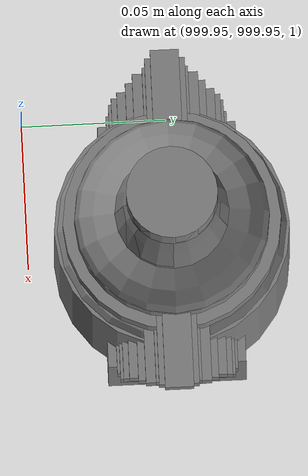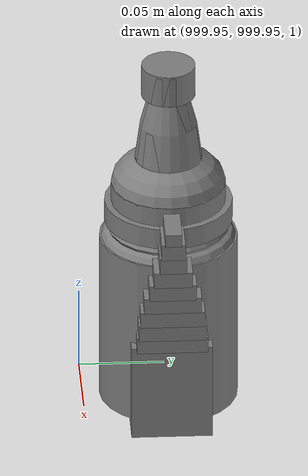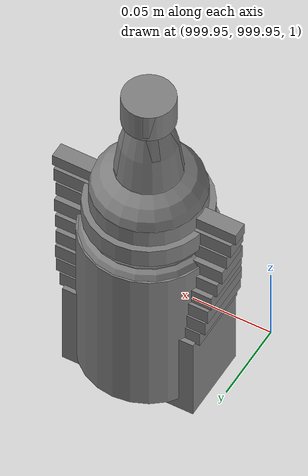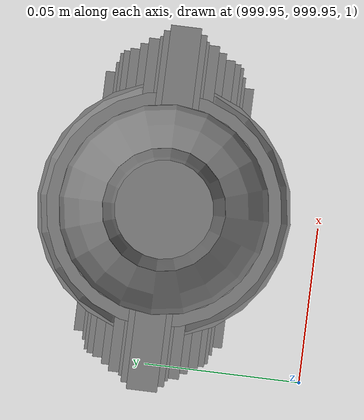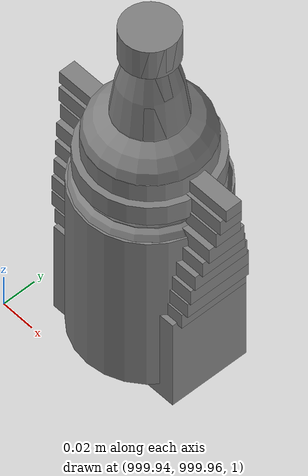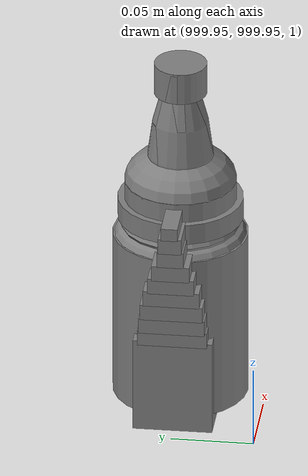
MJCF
<mujoco>
    <option gravity="0.000000000 0.000000000 -9.810000420" timestep="0.0166666" integrator="implicitfast" density="1.225" viscosity="1.8000001e-05" noslip_iterations="10" iterations="100" sdf_iterations="50">
        <flag multiccd="disable"/>
    </option>
    <size memory="1000M"/>
    <compiler coordinate="local"/>
    <worldbody>
        <light cutoff="30" pos="0 1 1" dir="0 -1 -2"/>
        <light cutoff="30" pos="0 -1 1" dir="0 1 -2"/>
        <body pos="0.000000000 0.000000000 0.000000000" euler="0.000000000 0.000000000 0.000000000" name="Interactive Objects_Interactive Objects"/>
        <body pos="1000.000000000 1000.000000000 1.000000000" euler="0.000000000 0.000000000 0.000000000" name="openloong_gripper_2f85_fix_base_usda_bottle_blue">
            <geom contype="1" conaffinity="1" density="1000" type="ellipsoid" material="" rgba="0.500000000 0.500000000 0.500000000 1.000000000" solimp="0.899999976 0.949999988 0.001000000" friction="1.000000000 0.005000000 0.000100000" solref="0.020000000 1.000000000" margin="0" condim="3" group="0" pos="0.000000000 0.000000000 0.118920922" quat="1.000000000 0.000000000 0.000000000 0.000000000" size="0.030999999 0.030999999 0.029999999" name="openloong_gripper_2f85_fix_base_usda_geom_B4905548_2B22_4840_AA1B_91C3856D30F1"/>
            <geom contype="1" conaffinity="1" density="1000" type="box" material="" rgba="0.500000000 0.500000000 0.500000000 1.000000000" solimp="0.899999976 0.949999988 0.001000000" friction="1.000000000 0.005000000 0.000100000" solref="0.020000000 1.000000000" margin="0" condim="3" group="0" pos="0.000000000 0.000000000 0.002164602" quat="1.000000000 0.000000000 0.000000000 0.000000000" size="0.020000000 0.020000000 0.003000000" name="openloong_gripper_2f85_fix_base_usda_geom_529B60CE_0F38_4510_A236_0A63DBCAE8C2"/>
            <geom contype="1" conaffinity="1" density="1000" type="cylinder" material="" rgba="0.500000000 0.500000000 0.500000000 1.000000000" solimp="0.899999976 0.949999988 0.001000000" friction="1.000000000 0.005000000 0.000100000" solref="0.020000000 1.000000000" margin="0" condim="3" group="0" pos="0.000000000 -0.000366211 0.060859680" quat="1.000000000 0.000000000 0.000000000 0.000000000" size="0.030999999 0.057999998 1.000000000" name="openloong_gripper_2f85_fix_base_usda_geom_37768962_B43E_4D76_9D6C_770B2D862906"/>
            <geom contype="1" conaffinity="1" density="1000" type="cylinder" material="" rgba="0.500000000 0.500000000 0.500000000 1.000000000" solimp="0.899999976 0.949999988 0.001000000" friction="1.000000000 0.005000000 0.000100000" solref="0.020000000 1.000000000" margin="0" condim="3" group="0" pos="0.000000000 0.000000000 0.220594406" quat="1.000000000 0.000000000 0.000000000 0.000000000" size="0.016000001 0.010000000 1.000000000" name="openloong_gripper_2f85_fix_base_usda_geom_4053F830_99C8_48F6_B8AE_996E1597ADDA"/>
            <geom contype="1" conaffinity="1" density="1000" type="ellipsoid" material="" rgba="0.500000000 0.500000000 0.500000000 1.000000000" solimp="0.899999976 0.949999988 0.001000000" friction="1.000000000 0.005000000 0.000100000" solref="0.020000000 1.000000000" margin="0" condim="3" group="0" pos="0.000000000 0.000000000 0.144259930" quat="1.000000000 0.000000000 0.000000000 0.000000000" size="0.021000000 0.021000000 0.079999998" name="openloong_gripper_2f85_fix_base_usda_geom_E1FF61BF_12E5_4F74_86E4_BD5A0988E5E3"/>
            <freejoint name="openloong_gripper_2f85_fix_base_usda_bottle_blue_joint"/>
            <site size="0.005000000 0.005000000 0.005000000" rgba="0.500000000 0.500000000 0.500000000 1.000000000" pos="0.000000000 0.000000000 0.000000000" quat="0.999961913 0.008726535 0.000000000 0.000000000" group="0" type="sphere" name="openloong_gripper_2f85_fix_base_usda_bottle_bluesite"/>
        </body>
        <body pos="1000.000000000 1000.000000000 1.000000000" euler="0.000000000 0.000000000 0.000000000" name="openloong_gripper_2f85_fix_base_usda_jar_01">
            <geom contype="1" conaffinity="1" density="1000" type="box" material="" rgba="0.500000000 0.500000000 0.500000000 1.000000000" solimp="0.899999976 0.949999988 0.001000000" friction="1.000000000 0.005000000 0.000100000" solref="0.020000000 1.000000000" margin="0" condim="3" group="0" pos="0.000000000 0.000000000 0.006158113" quat="1.000000000 0.000000000 0.000000000 0.000000000" size="0.020000000 0.020000000 0.005000000" name="openloong_gripper_2f85_fix_base_usda_geom_FEFD5852_E562_4D60_B401_38BE72CD85AE"/>
            <geom contype="1" conaffinity="1" density="1000" type="cylinder" material="" rgba="0.500000000 0.500000000 0.500000000 1.000000000" solimp="0.899999976 0.949999988 0.001000000" friction="1.000000000 0.005000000 0.000100000" solref="0.020000000 1.000000000" margin="0" condim="3" group="0" pos="0.000000000 0.000000000 0.062744498" quat="1.000000000 0.000000000 0.000000000 0.000000000" size="0.041000001 0.052999999 1.000000000" name="openloong_gripper_2f85_fix_base_usda_geom_390A63A3_4FDB_4DFF_9977_107611C43528"/>
            <geom contype="1" conaffinity="1" density="1000" type="ellipsoid" material="" rgba="0.500000000 0.500000000 0.500000000 1.000000000" solimp="0.899999976 0.949999988 0.001000000" friction="1.000000000 0.005000000 0.000100000" solref="0.020000000 1.000000000" margin="0" condim="3" group="0" pos="0.000000000 0.000000000 0.122252703" quat="1.000000000 0.000000000 0.000000000 0.000000000" size="0.035999998 0.035999998 0.010000000" name="openloong_gripper_2f85_fix_base_usda_geom_8F36B609_F799_496E_AF60_3369F43B3D48"/>
            <geom contype="1" conaffinity="1" density="1000" type="cylinder" material="" rgba="0.500000000 0.500000000 0.500000000 1.000000000" solimp="0.899999976 0.949999988 0.001000000" friction="1.000000000 0.005000000 0.000100000" solref="0.020000000 1.000000000" margin="0" condim="3" group="0" pos="0.000000000 0.000000000 0.015747190" quat="1.000000000 0.000000000 0.000000000 0.000000000" size="0.035000000 0.010000000 1.000000000" name="openloong_gripper_2f85_fix_base_usda_geom_4C797C89_D6E9_4C5E_8043_7BAD11F6C8BC"/>
            <geom contype="1" conaffinity="1" density="1000" type="ellipsoid" material="" rgba="0.500000000 0.500000000 0.500000000 1.000000000" solimp="0.899999976 0.949999988 0.001000000" friction="1.000000000 0.005000000 0.000100000" solref="0.020000000 1.000000000" margin="0" condim="3" group="0" pos="0.000000000 0.000000000 0.115815401" quat="1.000000000 0.000000000 0.000000000 0.000000000" size="0.039999999 0.039999999 0.010000000" name="openloong_gripper_2f85_fix_base_usda_geom_38108DE8_AD9A_4A6B_8F54_FCAF802B8A47"/>
            <geom contype="1" conaffinity="1" density="1000" type="cylinder" material="" rgba="0.500000000 0.500000000 0.500000000 1.000000000" solimp="0.899999976 0.949999988 0.001000000" friction="1.000000000 0.005000000 0.000100000" solref="0.020000000 1.000000000" margin="0" condim="3" group="0" pos="0.000000000 0.000000000 0.133183479" quat="1.000000000 0.000000000 0.000000000 0.000000000" size="0.037999999 0.006500000 1.000000000" name="openloong_gripper_2f85_fix_base_usda_geom_CBB4B76B_2235_461A_854F_487A80E99898"/>
            <freejoint name="openloong_gripper_2f85_fix_base_usda_jar_01_joint"/>
            <site size="0.005000000 0.005000000 0.005000000" rgba="0.500000000 0.500000000 0.500000000 1.000000000" pos="0.000000000 0.000000000 0.000000000" quat="1.000000000 0.000000000 0.000000000 0.000000000" group="0" type="sphere" name="openloong_gripper_2f85_fix_base_usda_jar_01site"/>
        </body>
        <body pos="-2.142006636 5.811167240 1.704612494" euler="-106.253021240 -46.956504822 11.645406723" mocap="true" name="spotlight4_SpotLight"/>
        <body pos="1000.000000000 1000.000000000 1.000000000" euler="0.000000000 0.000000000 0.000000000" name="openloong_gripper_2f85_fix_base_usda_salt">
            <geom contype="1" conaffinity="1" density="1000" type="box" material="" rgba="0.500000000 0.500000000 0.500000000 1.000000000" solimp="0.899999976 0.949999988 0.001000000" friction="1.000000000 0.005000000 0.000100000" solref="0.020000000 1.000000000" margin="0" condim="3" group="0" pos="0.000305176 0.000000000 0.084862232" quat="1.000000000 0.000000000 0.000000000 0.000000000" size="0.048999999 0.018999999 0.005000000" name="openloong_gripper_2f85_fix_base_usda_geom_8A9B55E4_B55C_4676_BC93_100C5DF2C02B"/>
            <geom contype="1" conaffinity="1" density="1000" type="box" material="" rgba="0.500000000 0.500000000 0.500000000 1.000000000" solimp="0.899999976 0.949999988 0.001000000" friction="1.000000000 0.005000000 0.000100000" solref="0.020000000 1.000000000" margin="0" condim="3" group="0" pos="0.000305176 0.000000000 0.104564309" quat="1.000000000 0.000000000 0.000000000 0.000000000" size="0.052000001 0.014000000 0.005000000" name="openloong_gripper_2f85_fix_base_usda_geom_94A5B644_A423_4C60_9204_2E81617200F8"/>
            <geom contype="1" conaffinity="1" density="1000" type="box" material="" rgba="0.500000000 0.500000000 0.500000000 1.000000000" solimp="0.899999976 0.949999988 0.001000000" friction="1.000000000 0.005000000 0.000100000" solref="0.020000000 1.000000000" margin="0" condim="3" group="0" pos="0.000305176 0.000000000 0.114487171" quat="1.000000000 0.000000000 0.000000000 0.000000000" size="0.054000001 0.011500000 0.005000000" name="openloong_gripper_2f85_fix_base_usda_geom_CFBD978D_1F22_4715_B4E6_334AF8D28167"/>
            <geom contype="1" conaffinity="1" density="1000" type="box" material="" rgba="0.500000000 0.500000000 0.500000000 1.000000000" solimp="0.899999976 0.949999988 0.001000000" friction="1.000000000 0.005000000 0.000100000" solref="0.020000000 1.000000000" margin="0" condim="3" group="0" pos="0.000305176 0.000000000 0.075103164" quat="1.000000000 0.000000000 0.000000000 0.000000000" size="0.048000000 0.020000000 0.005000000" name="openloong_gripper_2f85_fix_base_usda_geom_0423D83C_9F82_44D1_B0D3_078DFF44D31E"/>
            <geom contype="1" conaffinity="1" density="1000" type="box" material="" rgba="0.500000000 0.500000000 0.500000000 1.000000000" solimp="0.899999976 0.949999988 0.001000000" friction="1.000000000 0.005000000 0.000100000" solref="0.020000000 1.000000000" margin="0" condim="3" group="0" pos="0.000305176 0.000000000 0.134892464" quat="1.000000000 0.000000000 0.000000000 0.000000000" size="0.057000000 0.007000000 0.005000000" name="openloong_gripper_2f85_fix_base_usda_geom_F84CB4A8_E74A_4E5C_9648_8A660EDF1CA3"/>
            <geom contype="1" conaffinity="1" density="1000" type="box" material="" rgba="0.500000000 0.500000000 0.500000000 1.000000000" solimp="0.899999976 0.949999988 0.001000000" friction="1.000000000 0.005000000 0.000100000" solref="0.020000000 1.000000000" margin="0" condim="3" group="0" pos="0.000305176 0.000000000 0.094920278" quat="1.000000000 0.000000000 0.000000000 0.000000000" size="0.050000001 0.017000001 0.005000000" name="openloong_gripper_2f85_fix_base_usda_geom_710B5A26_FECF_4874_8ADC_2767ED1D460C"/>
            <geom contype="1" conaffinity="1" density="1000" type="box" material="" rgba="0.500000000 0.500000000 0.500000000 1.000000000" solimp="0.899999976 0.949999988 0.001000000" friction="1.000000000 0.005000000 0.000100000" solref="0.020000000 1.000000000" margin="0" condim="3" group="0" pos="0.000305176 0.000000000 0.065204859" quat="1.000000000 0.000000000 0.000000000 0.000000000" size="0.045000002 0.021000000 0.005000000" name="openloong_gripper_2f85_fix_base_usda_geom_C541B246_D7BB_4EF6_BB68_2DDFCCBF4FE9"/>
            <geom contype="1" conaffinity="1" density="1000" type="box" material="" rgba="0.500000000 0.500000000 0.500000000 1.000000000" solimp="0.899999976 0.949999988 0.001000000" friction="1.000000000 0.005000000 0.000100000" solref="0.020000000 1.000000000" margin="0" condim="3" group="0" pos="0.000305176 0.000000000 0.144135714" quat="1.000000000 0.000000000 0.000000000 0.000000000" size="0.059000000 0.005000000 0.004000000" name="openloong_gripper_2f85_fix_base_usda_geom_5C3BDAD3_4D92_4048_9079_1C5CA56088E5"/>
            <geom contype="1" conaffinity="1" density="1000" type="box" material="" rgba="0.500000000 0.500000000 0.500000000 1.000000000" solimp="0.899999976 0.949999988 0.001000000" friction="1.000000000 0.005000000 0.000100000" solref="0.020000000 1.000000000" margin="0" condim="3" group="0" pos="0.000000000 0.000000000 0.031593561" quat="1.000000000 0.000000000 0.000000000 0.000000000" size="0.041999999 0.024000000 0.029999999" name="openloong_gripper_2f85_fix_base_usda_geom_3A0021A6_E426_48CC_9B81_DF1B8E6F8AFA"/>
            <geom contype="1" conaffinity="1" density="1000" type="box" material="" rgba="0.500000000 0.500000000 0.500000000 1.000000000" solimp="0.899999976 0.949999988 0.001000000" friction="1.000000000 0.005000000 0.000100000" solref="0.020000000 1.000000000" margin="0" condim="3" group="0" pos="0.000305176 0.000000000 0.124608755" quat="1.000000000 0.000000000 0.000000000 0.000000000" size="0.055000000 0.008000000 0.005000000" name="openloong_gripper_2f85_fix_base_usda_geom_C9530BCA_DB1F_4FD5_8D0E_F02418DD68E2"/>
            <freejoint name="openloong_gripper_2f85_fix_base_usda_salt_joint"/>
            <site size="0.005000000 0.005000000 0.005000000" rgba="0.500000000 0.500000000 0.500000000 1.000000000" pos="0.000000000 0.000000000 0.000000000" quat="1.000000000 0.000000000 0.000000000 0.000000000" group="0" type="sphere" name="openloong_gripper_2f85_fix_base_usda_saltsite"/>
        </body>
        <body pos="-2.267544031 5.765722752 1.836375356" euler="-140.737274170 55.321846008 -82.572692871" mocap="true" name="spotlight2_SpotLight"/>
        <body pos="-2.271486759 6.553732872 1.690982819" euler="70.781394958 88.956817627 154.477828979" mocap="true" name="spotlight6_SpotLight"/>
        <body pos="1000.000000000 1000.000000000 1.000000000" euler="0.000000000 0.000000000 0.000000000" name="openloong_gripper_2f85_fix_base_usda_bottle_red">
            <geom contype="1" conaffinity="1" density="1000" type="ellipsoid" material="" rgba="0.500000000 0.500000000 0.500000000 1.000000000" solimp="0.899999976 0.949999988 0.001000000" friction="1.000000000 0.005000000 0.000100000" solref="0.020000000 1.000000000" margin="0" condim="3" group="0" pos="0.000000000 0.000000000 0.144284487" quat="1.000000000 0.000000000 0.000000000 0.000000000" size="0.021000000 0.021000000 0.079999998" name="openloong_gripper_2f85_fix_base_usda_geom_88EC940A_A945_4894_9E00_7BDECC1E0FB7"/>
            <geom contype="1" conaffinity="1" density="1000" type="cylinder" material="" rgba="0.500000000 0.500000000 0.500000000 1.000000000" solimp="0.899999976 0.949999988 0.001000000" friction="1.000000000 0.005000000 0.000100000" solref="0.020000000 1.000000000" margin="0" condim="3" group="0" pos="0.000000000 0.000000000 0.220618963" quat="1.000000000 0.000000000 0.000000000 0.000000000" size="0.016000001 0.010000000 1.000000000" name="openloong_gripper_2f85_fix_base_usda_geom_733B772C_E4CA_45AA_B0DB_E73F6F3587D1"/>
            <geom contype="1" conaffinity="1" density="1000" type="ellipsoid" material="" rgba="0.500000000 0.500000000 0.500000000 1.000000000" solimp="0.899999976 0.949999988 0.001000000" friction="1.000000000 0.005000000 0.000100000" solref="0.020000000 1.000000000" margin="0" condim="3" group="0" pos="0.000000000 0.000000000 0.118945479" quat="1.000000000 0.000000000 0.000000000 0.000000000" size="0.030999999 0.030999999 0.029999999" name="openloong_gripper_2f85_fix_base_usda_geom_FFFDBFAD_6D23_4806_AF58_758DBD31AFE1"/>
            <geom contype="1" conaffinity="1" density="1000" type="box" material="" rgba="0.500000000 0.500000000 0.500000000 1.000000000" solimp="0.899999976 0.949999988 0.001000000" friction="1.000000000 0.005000000 0.000100000" solref="0.020000000 1.000000000" margin="0" condim="3" group="0" pos="0.000000000 0.000000000 0.002189159" quat="1.000000000 0.000000000 0.000000000 0.000000000" size="0.020000000 0.020000000 0.003000000" name="openloong_gripper_2f85_fix_base_usda_geom_4D305E52_2BF9_4740_B773_11973D79FB56"/>
            <geom contype="1" conaffinity="1" density="1000" type="cylinder" material="" rgba="0.500000000 0.500000000 0.500000000 1.000000000" solimp="0.899999976 0.949999988 0.001000000" friction="1.000000000 0.005000000 0.000100000" solref="0.020000000 1.000000000" margin="0" condim="3" group="0" pos="0.000000000 -0.000366211 0.060884237" quat="1.000000000 0.000000000 0.000000000 0.000000000" size="0.030999999 0.057999998 1.000000000" name="openloong_gripper_2f85_fix_base_usda_geom_3DAF7A94_A909_4128_A0BA_5C692289D2C2"/>
            <freejoint name="openloong_gripper_2f85_fix_base_usda_bottle_red_joint"/>
            <site size="0.005000000 0.005000000 0.005000000" rgba="0.500000000 0.500000000 0.500000000 1.000000000" pos="0.000000000 0.000000000 0.000000000" quat="0.999961913 0.008726535 0.000000000 0.000000000" group="0" type="sphere" name="openloong_gripper_2f85_fix_base_usda_bottle_redsite"/>
        </body>
        <body pos="1000.000000000 1000.000000000 1.000000000" euler="0.000000000 0.000000000 0.000000000" name="openloong_gripper_2f85_fix_base_usda_can">
            <geom contype="1" conaffinity="1" density="1000" type="cylinder" material="" rgba="0.500000000 0.500000000 0.500000000 1.000000000" solimp="0.899999976 0.949999988 0.001000000" friction="1.000000000 0.005000000 0.000100000" solref="0.020000000 1.000000000" margin="0" condim="3" group="0" pos="0.000000000 0.000000000 0.079676986" quat="1.000000000 0.000000000 0.000000000 0.000000000" size="0.034000002 0.071999997 1.000000000" name="openloong_gripper_2f85_fix_base_usda_geom_578B6C53_F4C8_40AF_8F26_FC4F7FF1B273"/>
            <geom contype="1" conaffinity="1" density="1000" type="ellipsoid" material="" rgba="0.500000000 0.500000000 0.500000000 1.000000000" solimp="0.899999976 0.949999988 0.001000000" friction="1.000000000 0.005000000 0.000100000" solref="0.020000000 1.000000000" margin="0" condim="3" group="0" pos="0.000000000 0.000000000 0.151854277" quat="1.000000000 0.000000000 0.000000000 0.000000000" size="0.034000002 0.034000002 0.020000000" name="openloong_gripper_2f85_fix_base_usda_geom_8E2C3E82_790C_4DC6_A20F_C15B0592665A"/>
            <geom contype="1" conaffinity="1" density="1000" type="box" material="" rgba="0.500000000 0.500000000 0.500000000 1.000000000" solimp="0.899999976 0.949999988 0.001000000" friction="1.000000000 0.005000000 0.000100000" solref="0.020000000 1.000000000" margin="0" condim="3" group="0" pos="0.000000000 0.000000000 0.004777670" quat="1.000000000 0.000000000 0.000000000 0.000000000" size="0.020000000 0.020000000 0.005000000" name="openloong_gripper_2f85_fix_base_usda_geom_C671E94D_689C_4BF3_B44B_6A4BFEC62C37"/>
            <freejoint name="openloong_gripper_2f85_fix_base_usda_can_joint"/>
            <site size="0.005000000 0.005000000 0.005000000" rgba="0.500000000 0.500000000 0.500000000 1.000000000" pos="0.000000000 0.000000000 0.000000000" quat="1.000000000 0.000000000 0.000000000 0.000000000" group="0" type="sphere" name="openloong_gripper_2f85_fix_base_usda_cansite"/>
        </body>
        <body pos="0.000000000 0.000000000 0.000000000" euler="0.000000000 0.000000000 0.000000000" name=" Static Objects_ Static Objects">
            <geom contype="1" conaffinity="1" density="1000" type="box" material="" rgba="0.500000000 0.500000000 0.500000000 1.000000000" solimp="0.899999976 0.949999988 0.001000000" friction="1.000000000 0.005000000 0.000100000" solref="0.020000000 1.000000000" margin="0" condim="3" group="0" pos="-6.286010742 6.153595448 1.563861728" quat="0.707107067 0.000000000 0.000000000 0.707106471" size="0.529999971 3.134999990 0.025000000" name=" Static Objects_geom_AE11C1F3_1C46_4309_B398_938990759BDA"/>
            <geom contype="1" conaffinity="1" density="1000" type="box" material="" rgba="0.500000000 0.500000000 0.500000000 1.000000000" solimp="0.899999976 0.949999988 0.001000000" friction="1.000000000 0.005000000 0.000100000" solref="0.020000000 1.000000000" margin="0" condim="3" group="0" pos="-3.101639986 6.150595188 1.018643856" quat="1.000000000 0.000000000 0.000000000 0.000000000" size="0.050000001 0.579999983 1.019999981" name=" Static Objects_geom_53A0A6A6_CB20_46A8_855E_5B315A906355"/>
            <geom contype="1" conaffinity="1" density="1000" type="box" material="" rgba="0.500000000 0.500000000 0.500000000 1.000000000" solimp="0.899999976 0.949999988 0.001000000" friction="1.000000000 0.005000000 0.000100000" solref="0.020000000 1.000000000" margin="0" condim="3" group="0" pos="-2.825197220 6.153595448 1.563861728" quat="0.707107067 0.000000000 0.000000000 0.707106471" size="0.550000012 0.239999995 0.025000000" name=" Static Objects_geom_B4A28C3C_50BC_4238_BCF0_B4077F823893"/>
            <geom contype="1" conaffinity="1" density="1000" type="box" material="" rgba="0.500000000 0.500000000 0.500000000 1.000000000" solimp="0.899999976 0.949999988 0.001000000" friction="1.000000000 0.005000000 0.000100000" solref="0.020000000 1.000000000" margin="0" condim="3" group="0" pos="-6.311686516 6.153595448 1.018643856" quat="0.707107067 0.000000000 0.000000000 0.707106471" size="0.050000001 3.150000095 1.019999981" name=" Static Objects_geom_3F2BF54B_DD89_460E_8E97_B477C400B344"/>
            <geom contype="1" conaffinity="1" density="1000" type="box" material="" rgba="0.500000000 0.500000000 0.500000000 1.000000000" solimp="0.899999976 0.949999988 0.001000000" friction="1.000000000 0.005000000 0.000100000" solref="0.020000000 1.000000000" margin="0" condim="3" group="0" pos="-2.825197220 6.153595448 1.115278244" quat="0.707107067 0.000000000 0.000000000 0.707106471" size="0.550000012 0.239999995 0.025000000" name=" Static Objects_geom_410CE847_586F_49B6_9731_6CBD54130F9A"/>
            <geom contype="1" conaffinity="1" density="1000" type="box" material="" rgba="0.500000000 0.500000000 0.500000000 1.000000000" solimp="0.899999976 0.949999988 0.001000000" friction="1.000000000 0.005000000 0.000100000" solref="0.020000000 1.000000000" margin="0" condim="3" group="0" pos="-6.293097973 6.153595448 1.114443064" quat="0.707107067 0.000000000 0.000000000 0.707106471" size="0.529999971 3.134999990 0.025000000" name=" Static Objects_geom_48F51D9D_A1A1_40C6_BA38_EE61CF7C9192"/>
            <geom contype="1" conaffinity="1" density="1000" type="box" material="" rgba="0.500000000 0.500000000 0.500000000 1.000000000" solimp="0.899999976 0.949999988 0.001000000" friction="1.000000000 0.005000000 0.000100000" solref="0.020000000 1.000000000" margin="0" condim="3" group="0" pos="-2.825197220 6.153595448 0.629031777" quat="0.707107067 0.000000000 0.000000000 0.707106471" size="0.550000012 0.239999995 0.025000000" name=" Static Objects_geom_380615E6_FDD6_402F_BC09_E8174D3AE0E6"/>
            <geom contype="1" conaffinity="1" density="1000" type="box" material="" rgba="0.500000000 0.500000000 0.500000000 1.000000000" solimp="0.899999976 0.949999988 0.001000000" friction="1.000000000 0.005000000 0.000100000" solref="0.020000000 1.000000000" margin="0" condim="3" group="0" pos="-6.286010742 6.153595448 0.096129179" quat="0.707107067 0.000000000 0.000000000 0.707106471" size="0.529999971 3.134999990 0.098999999" name=" Static Objects_geom_ECB2BA31_BB6C_4F47_9E35_FA136D4C41D6"/>
            <geom contype="1" conaffinity="1" density="1000" type="box" material="" rgba="0.500000000 0.500000000 0.500000000 1.000000000" solimp="0.899999976 0.949999988 0.001000000" friction="1.000000000 0.005000000 0.000100000" solref="0.020000000 1.000000000" margin="0" condim="3" group="0" pos="-2.825197220 6.153595448 0.097434282" quat="0.707107067 0.000000000 0.000000000 0.707106471" size="0.550000012 0.239999995 0.098999999" name=" Static Objects_geom_3BA53A21_F45E_4714_873C_FAE47412C8A5"/>
            <geom contype="1" conaffinity="1" density="1000" type="box" material="" rgba="0.500000000 0.500000000 0.500000000 1.000000000" solimp="0.899999976 0.949999988 0.001000000" friction="1.000000000 0.005000000 0.000100000" solref="0.020000000 1.000000000" margin="0" condim="3" group="0" pos="-6.286010742 6.153595448 0.629031777" quat="0.707107067 0.000000000 0.000000000 0.707106471" size="0.529999971 3.134999990 0.025000000" name=" Static Objects_geom_4EA18584_704A_420A_89BA_BAC368DECF7E"/>
            <geom contype="1" conaffinity="1" density="1000" type="box" material="" rgba="0.500000000 0.500000000 0.500000000 1.000000000" solimp="0.899999976 0.949999988 0.001000000" friction="1.000000000 0.005000000 0.000100000" solref="0.020000000 1.000000000" margin="0" condim="3" group="0" pos="-6.000000000 20.159999847 2.000000000" quat="1.000000000 0.000000000 0.000000000 0.000000000" size="6.079999924 0.070000000 2.000000000" name=" Static Objects_geom_1149DDF1_0BC9_4575_9572_466A9190C6CA"/>
            <geom contype="1" conaffinity="1" density="1000" type="box" material="" rgba="0.500000000 0.500000000 0.500000000 1.000000000" solimp="0.899999976 0.949999988 0.001000000" friction="1.000000000 0.005000000 0.000100000" solref="0.020000000 1.000000000" margin="0" condim="3" group="0" pos="-6.000000000 0.035000000 2.000000000" quat="1.000000000 0.000000000 0.000000000 0.000000000" size="6.079999924 0.070000000 2.000000000" name=" Static Objects_geom_7CF82B4E_B690_4BF6_8E01_C9BBC1C0C31E"/>
            <geom contype="1" conaffinity="1" density="1000" type="box" material="" rgba="0.500000000 0.500000000 0.500000000 1.000000000" solimp="0.899999976 0.949999988 0.001000000" friction="1.000000000 0.005000000 0.000100000" solref="0.020000000 1.000000000" margin="0" condim="3" group="0" pos="0.000000000 10.000000000 2.000000000" quat="1.000000000 0.000000000 0.000000000 0.000000000" size="0.070000000 10.500000000 2.000000000" name=" Static Objects_geom_63CF30B9_7713_435C_BA54_6B4F2336DE55"/>
            <geom contype="1" conaffinity="1" density="1000" type="box" material="" rgba="0.500000000 0.500000000 0.500000000 1.000000000" solimp="0.899999976 0.949999988 0.001000000" friction="1.000000000 0.005000000 0.000100000" solref="0.020000000 1.000000000" margin="0" condim="3" group="0" pos="-12.050000191 10.000000000 2.000000000" quat="1.000000000 0.000000000 0.000000000 0.000000000" size="0.070000000 10.500000000 2.000000000" name=" Static Objects_geom_BEFAD560_D0B7_4356_A6E7_64BC5307BEA1"/>
            <geom contype="1" conaffinity="1" density="1000" type="plane" material="" rgba="0.500000000 0.500000000 0.500000000 1.000000000" solimp="0.899999976 0.949999988 0.001000000" friction="1.000000000 0.005000000 0.000100000" solref="0.020000000 1.000000000" margin="0" condim="3" group="0" pos="-6.000000000 10.399999619 0.000000000" quat="1.000000000 0.000000000 0.000000000 0.000000000" size="6.050000191 10.800000191 0.010000000" name=" Static Objects_geom_E0E32270_0ADF_469D_990A_B03F8FB90453"/>
            <geom contype="1" conaffinity="1" density="1000" type="box" material="" rgba="0.500000000 0.500000000 0.500000000 1.000000000" solimp="0.899999976 0.949999988 0.001000000" friction="1.000000000 0.005000000 0.000100000" solref="0.020000000 1.000000000" margin="0" condim="3" group="0" pos="-8.830721855 2.096410990 0.549305558" quat="1.000000000 0.000000000 0.000000000 0.000000000" size="0.280000001 0.430000007 0.550000012" name=" Static Objects_geom_1362B8B0_87E8_4BB5_B5B9_37F4D7309291"/>
            <geom contype="1" conaffinity="1" density="1000" type="box" material="" rgba="0.500000000 0.500000000 0.500000000 1.000000000" solimp="0.899999976 0.949999988 0.001000000" friction="1.000000000 0.005000000 0.000100000" solref="0.020000000 1.000000000" margin="0" condim="3" group="0" pos="-6.460197449 2.937205315 0.548931718" quat="1.000000000 0.000000000 0.000000000 0.000000000" size="2.650000095 0.430000007 0.550000012" name=" Static Objects_geom_481588F6_D795_45ED_98FA_3A92C719EC7F"/>
            <geom contype="1" conaffinity="1" density="1000" type="box" material="" rgba="0.500000000 0.500000000 0.500000000 1.000000000" solimp="0.899999976 0.949999988 0.001000000" friction="1.000000000 0.005000000 0.000100000" solref="0.020000000 1.000000000" margin="0" condim="3" group="0" pos="-4.240264893 1.327049494 0.549888909" quat="1.000000000 0.000000000 0.000000000 0.000000000" size="0.430000007 1.200000048 0.550000012" name=" Static Objects_geom_CFFF18F5_0FB1_43F3_AEF1_A78893DCE851"/>
            <geom contype="1" conaffinity="1" density="1000" type="box" material="" rgba="0.500000000 0.500000000 0.500000000 1.000000000" solimp="0.899999976 0.949999988 0.001000000" friction="1.000000000 0.005000000 0.000100000" solref="0.020000000 1.000000000" margin="0" condim="3" group="0" pos="-7.408766270 3.088089943 1.776644945" quat="0.928051054 0.000000000 0.000000000 0.372453064" size="0.050000001 0.100000001 0.050000001" name=" Static Objects_geom_1680EF08_384E_48A2_BA6F_9F1A7A0B909C"/>
            <geom contype="1" conaffinity="1" density="1000" type="box" material="" rgba="0.500000000 0.500000000 0.500000000 1.000000000" solimp="0.899999976 0.949999988 0.001000000" friction="1.000000000 0.005000000 0.000100000" solref="0.020000000 1.000000000" margin="0" condim="3" group="0" pos="-7.437745571 3.067511320 1.289965630" quat="1.000000000 0.000000000 0.000000000 0.000000000" size="0.029999999 0.020000000 0.020000000" name=" Static Objects_geom_1EA6AE56_0569_4366_9010_9B2E892C110F"/>
            <geom contype="1" conaffinity="1" density="1000" type="box" material="" rgba="0.500000000 0.500000000 0.500000000 1.000000000" solimp="0.899999976 0.949999988 0.001000000" friction="1.000000000 0.005000000 0.000100000" solref="0.020000000 1.000000000" margin="0" condim="3" group="0" pos="-7.719123363 2.867671013 1.173410416" quat="1.000000000 0.000000000 0.000000000 0.000000000" size="0.250000000 0.250000000 0.079999998" name=" Static Objects_geom_9CA44B6F_94A6_438E_89C9_936E00F93732"/>
            <geom contype="1" conaffinity="1" density="1000" type="box" material="" rgba="0.500000000 0.500000000 0.500000000 1.000000000" solimp="0.899999976 0.949999988 0.001000000" friction="1.000000000 0.005000000 0.000100000" solref="0.020000000 1.000000000" margin="0" condim="3" group="0" pos="-7.719123363 2.958004713 1.530241251" quat="1.000000000 0.000000000 0.000000000 0.000000000" size="0.250000000 0.159999996 0.280000001" name=" Static Objects_geom_18625547_5E78_4544_81D6_9C2DD906877B"/>
            <geom contype="1" conaffinity="1" density="1000" type="cylinder" material="" rgba="0.500000000 0.500000000 0.500000000 1.000000000" solimp="0.899999976 0.949999988 0.001000000" friction="1.000000000 0.005000000 0.000100000" solref="0.020000000 1.000000000" margin="0" condim="3" group="0" pos="-7.427312374 3.069516420 1.502544641" quat="0.928051054 0.000000000 0.000000000 0.372453064" size="0.015000000 0.230000004 0.100000001" name=" Static Objects_geom_C9D2E97F_2C9D_4107_9A6B_9D425555344E"/>
            <geom contype="1" conaffinity="1" density="1000" type="box" material="" rgba="0.500000000 0.500000000 0.500000000 1.000000000" solimp="0.899999976 0.949999988 0.001000000" friction="1.000000000 0.005000000 0.000100000" solref="0.020000000 1.000000000" margin="0" condim="3" group="0" pos="-9.058088303 6.434794426 1.209077358" quat="1.000000000 0.000000000 0.000000000 0.000000000" size="0.250000000 0.100000001 0.070000000" name=" Static Objects_geom_28C5A169_70DC_450F_A938_411D84AD4E74"/>
            <geom contype="1" conaffinity="1" density="1000" type="box" material="" rgba="0.500000000 0.500000000 0.500000000 1.000000000" solimp="0.899999976 0.949999988 0.001000000" friction="1.000000000 0.005000000 0.000100000" solref="0.020000000 1.000000000" margin="0" condim="3" group="0" pos="-5.611940861 6.318420410 0.350975692" quat="1.000000000 0.000000000 0.000000000 0.000000000" size="0.699999988 0.100000001 0.150000006" name=" Static Objects_geom_80916A07_69BD_44B6_966B_0C78C687C003"/>
            <geom contype="1" conaffinity="1" density="1000" type="box" material="" rgba="0.500000000 0.500000000 0.500000000 1.000000000" solimp="0.899999976 0.949999988 0.001000000" friction="1.000000000 0.005000000 0.000100000" solref="0.020000000 1.000000000" margin="0" condim="3" group="0" pos="-9.237723351 6.464855671 1.209077358" quat="1.000000000 0.000000000 0.000000000 0.000000000" size="0.100000001 0.100000001 0.070000000" name=" Static Objects_geom_61D20893_1A3C_435C_A012_701105CF2210"/>
            <geom contype="1" conaffinity="1" density="1000" type="box" material="" rgba="0.500000000 0.500000000 0.500000000 1.000000000" solimp="0.899999976 0.949999988 0.001000000" friction="1.000000000 0.005000000 0.000100000" solref="0.020000000 1.000000000" margin="0" condim="3" group="0" pos="-6.300771236 6.459744930 1.744376063" quat="1.000000000 0.000000000 0.000000000 0.000000000" size="3.000000000 0.200000003 0.150000006" name=" Static Objects_geom_2F685DFF_0703_4CEB_9C1A_8DDC75CD3D15"/>
            <geom contype="1" conaffinity="1" density="1000" type="box" material="" rgba="0.500000000 0.500000000 0.500000000 1.000000000" solimp="0.899999976 0.949999988 0.001000000" friction="1.000000000 0.005000000 0.000100000" solref="0.020000000 1.000000000" margin="0" condim="3" group="0" pos="-7.373087406 6.458900928 1.214329123" quat="1.000000000 0.000000000 0.000000000 0.000000000" size="0.250000000 0.200000003 0.075000003" name=" Static Objects_geom_003C37D9_0192_4198_982B_384FEB3F70FA"/>
            <geom contype="1" conaffinity="1" density="1000" type="box" material="" rgba="0.500000000 0.500000000 0.500000000 1.000000000" solimp="0.899999976 0.949999988 0.001000000" friction="1.000000000 0.005000000 0.000100000" solref="0.020000000 1.000000000" margin="0" condim="3" group="0" pos="-4.035642624 6.459744930 0.352518857" quat="1.000000000 0.000000000 0.000000000 0.000000000" size="0.800000012 0.200000003 0.150000006" name=" Static Objects_geom_8E1C8370_92EE_452E_BCCC_50F8AD82F361"/>
            <geom contype="1" conaffinity="1" density="1000" type="box" material="" rgba="0.500000000 0.500000000 0.500000000 1.000000000" solimp="0.899999976 0.949999988 0.001000000" friction="1.000000000 0.005000000 0.000100000" solref="0.020000000 1.000000000" margin="0" condim="3" group="0" pos="-3.907610416 6.318625927 0.800981164" quat="1.000000000 0.000000000 0.000000000 0.000000000" size="0.500000000 0.100000001 0.150000006" name=" Static Objects_geom_CA7C01C8_37D6_4754_83EB_477959CEEA76"/>
            <geom contype="1" conaffinity="1" density="1000" type="box" material="" rgba="0.500000000 0.500000000 0.500000000 1.000000000" solimp="0.899999976 0.949999988 0.001000000" friction="1.000000000 0.005000000 0.000100000" solref="0.020000000 1.000000000" margin="0" condim="3" group="0" pos="-6.098561764 6.327973843 1.292199373" quat="1.000000000 0.000000000 0.000000000 0.000000000" size="0.500000000 0.100000001 0.150000006" name=" Static Objects_geom_C1D8AD06_3DBB_48B9_B8FE_1FA96BB2EF28"/>
            <geom contype="1" conaffinity="1" density="1000" type="box" material="" rgba="0.500000000 0.500000000 0.500000000 1.000000000" solimp="0.899999976 0.949999988 0.001000000" friction="1.000000000 0.005000000 0.000100000" solref="0.020000000 1.000000000" margin="0" condim="3" group="0" pos="-7.886891365 6.459744930 0.352518857" quat="1.000000000 0.000000000 0.000000000 0.000000000" size="1.500000000 0.200000003 0.150000006" name=" Static Objects_geom_FA6DC331_E2D9_4C8B_A480_714D910E3516"/>
            <geom contype="1" conaffinity="1" density="1000" type="box" material="" rgba="0.500000000 0.500000000 0.500000000 1.000000000" solimp="0.899999976 0.949999988 0.001000000" friction="1.000000000 0.005000000 0.000100000" solref="0.020000000 1.000000000" margin="0" condim="3" group="0" pos="-6.824534416 6.447464466 1.212718010" quat="1.000000000 0.000000000 0.000000000 0.000000000" size="0.100000001 0.100000001 0.075000003" name=" Static Objects_geom_4FAD7825_5BC1_4C3C_980C_CE7E020688EF"/>
            <geom contype="1" conaffinity="1" density="1000" type="box" material="" rgba="0.500000000 0.500000000 0.500000000 1.000000000" solimp="0.899999976 0.949999988 0.001000000" friction="1.000000000 0.005000000 0.000100000" solref="0.020000000 1.000000000" margin="0" condim="3" group="0" pos="-4.407354832 6.459744930 1.292199373" quat="1.000000000 0.000000000 0.000000000 0.000000000" size="1.240000010 0.200000003 0.150000006" name=" Static Objects_geom_9F770DC7_98B3_45A3_A058_CAD0EAC0DB60"/>
            <geom contype="1" conaffinity="1" density="1000" type="box" material="" rgba="0.500000000 0.500000000 0.500000000 1.000000000" solimp="0.899999976 0.949999988 0.001000000" friction="1.000000000 0.005000000 0.000100000" solref="0.020000000 1.000000000" margin="0" condim="3" group="0" pos="-6.751636982 6.459744930 0.800981164" quat="1.000000000 0.000000000 0.000000000 0.000000000" size="2.200000048 0.200000003 0.150000006" name=" Static Objects_geom_57B6F050_8CAB_454B_96FF_F264FF25B33C"/>
            <geom contype="1" conaffinity="1" density="1000" type="box" material="" rgba="0.500000000 0.500000000 0.500000000 1.000000000" solimp="0.899999976 0.949999988 0.001000000" friction="1.000000000 0.005000000 0.000100000" solref="0.020000000 1.000000000" margin="0" condim="3" group="0" pos="-6.924745083 6.362090111 1.214329123" quat="1.000000000 0.000000000 0.000000000 0.000000000" size="0.200000003 0.100000001 0.075000003" name=" Static Objects_geom_C1954BA1_ABE5_4633_A93C_095FBF8A5920"/>
            <geom contype="1" conaffinity="1" density="1000" type="box" material="" rgba="0.500000000 0.500000000 0.500000000 1.000000000" solimp="0.899999976 0.949999988 0.001000000" friction="1.000000000 0.005000000 0.000100000" solref="0.020000000 1.000000000" margin="0" condim="3" group="0" pos="-8.844120979 6.464855671 1.209077358" quat="1.000000000 0.000000000 0.000000000 0.000000000" size="0.100000001 0.100000001 0.070000000" name=" Static Objects_geom_8F55E606_3F24_45A1_A300_500D4D18E177"/>
            <geom contype="1" conaffinity="1" density="1000" type="box" material="" rgba="0.500000000 0.500000000 0.500000000 1.000000000" solimp="0.899999976 0.949999988 0.001000000" friction="1.000000000 0.005000000 0.000100000" solref="0.020000000 1.000000000" margin="0" condim="3" group="0" pos="-3.157672644 6.136868477 1.348373055" quat="1.000000000 0.000000000 0.000000000 0.000000000" size="0.200000003 0.519999981 0.300000012" name=" Static Objects_geom_C9564291_03D8_43CC_AB84_1B002140DF6E"/>
        </body>
        <body pos="-6.332345009 2.779978037 1.034067392" euler="0.000000000 0.000000000 0.000000000" name="openloong_gripper_2f85_fix_base_usda_basket">
            <geom contype="1" conaffinity="1" density="100000" type="box" material="" rgba="0.500000000 0.500000000 0.500000000 1.000000000" solimp="0.899999976 0.949999988 0.001000000" friction="1.000000000 0.899999976 0.000100000" solref="0.020000000 1.000000000" margin="0" condim="3" group="0" pos="-0.039724827 -0.188568115 0.167089701" quat="0.997537494 0.070135131 0.000000000 0.000000000" size="0.150000006 0.006000000 0.108000003" name="openloong_gripper_2f85_fix_base_usda_geom_8F0585C2_827F_4BEA_AC3B_13D183754254"/>
            <geom contype="1" conaffinity="1" density="100000" type="box" material="" rgba="0.500000000 0.500000000 0.500000000 1.000000000" solimp="0.899999976 0.949999988 0.001000000" friction="1.000000000 0.899999976 0.000100000" solref="0.020000000 1.000000000" margin="0" condim="3" group="0" pos="0.094372749 0.000000000 0.168361664" quat="0.706172049 0.036353335 0.036353379 0.706171215" size="0.200000003 0.006000000 0.108000003" name="openloong_gripper_2f85_fix_base_usda_geom_3E5602C8_E068_4E1E_AD4F_787A17C55B76"/>
            <geom contype="1" conaffinity="1" density="100000" type="box" material="" rgba="0.500000000 0.500000000 0.500000000 1.000000000" solimp="0.899999976 0.949999988 0.001000000" friction="1.000000000 0.899999976 0.000100000" solref="0.020000000 1.000000000" margin="0" condim="3" group="0" pos="-0.039724827 0.000000000 0.068126202" quat="1.000000000 0.000000000 0.000000000 0.000000000" size="0.129999995 0.174999997 0.006000000" name="openloong_gripper_2f85_fix_base_usda_geom_19B6F6DD_6B1E_43D7_9C98_A77B78000614"/>
            <geom contype="1" conaffinity="1" density="100000" type="box" material="" rgba="0.500000000 0.500000000 0.500000000 1.000000000" solimp="0.899999976 0.949999988 0.001000000" friction="1.000000000 0.899999976 0.000100000" solref="0.020000000 1.000000000" margin="0" condim="3" group="0" pos="-0.039724827 0.188377380 0.167089701" quat="0.997489929 -0.070808925 0.000000000 0.000000000" size="0.150000006 0.006000000 0.108000003" name="openloong_gripper_2f85_fix_base_usda_geom_26AC8D92_FDD9_48CE_9670_4BF657D2551F"/>
            <geom contype="1" conaffinity="1" density="100000" type="box" material="" rgba="0.500000000 0.500000000 0.500000000 1.000000000" solimp="0.899999976 0.949999988 0.001000000" friction="1.000000000 0.899999976 0.000100000" solref="0.020000000 1.000000000" margin="0" condim="3" group="0" pos="-0.172339439 0.000000000 0.168361664" quat="0.706172407 -0.036353018 -0.036353093 0.706170976" size="0.200000003 0.006000000 0.108000003" name="openloong_gripper_2f85_fix_base_usda_geom_B856DC8A_0B6D_438C_BFBF_9BD495E197AD"/>
            <freejoint name="openloong_gripper_2f85_fix_base_usda_basket_joint"/>
            <site size="0.005000000 0.005000000 0.005000000" rgba="0.500000000 0.500000000 0.500000000 1.000000000" pos="0.000000000 0.000000000 0.000000000" quat="1.000000000 0.000000000 0.000000000 0.000000000" group="0" type="sphere" name="openloong_gripper_2f85_fix_base_usda_basketsite"/>
        </body>
        <body pos="-3.510578632 3.403555870 -0.000000100" euler="0.000000000 0.000000000 40.200675964" name="openloong_gripper_2f85_fix_base_usda_PZ">
            <geom contype="1" conaffinity="1" density="1000" type="box" material="" rgba="0.500000000 0.500000000 0.500000000 1.000000000" solimp="0.899999976 0.949999988 0.001000000" friction="1.000000000 0.005000000 0.000100000" solref="0.020000000 1.000000000" margin="0" condim="3" group="0" pos="-0.047453165 0.056484699 0.373715430" quat="0.934750080 0.077914521 0.028795123 0.345459938" size="0.180000007 0.010000000 0.379999995" name="openloong_gripper_2f85_fix_base_usda_geom_F8297D9E_7785_47A9_939D_EC8530590870"/>
            <geom contype="1" conaffinity="1" density="1000" type="box" material="" rgba="0.500000000 0.500000000 0.500000000 1.000000000" solimp="0.899999976 0.949999988 0.001000000" friction="1.000000000 0.005000000 0.000100000" solref="0.020000000 1.000000000" margin="0" condim="3" group="0" pos="0.047452450 -0.054376602 0.374072611" quat="0.934387863 -0.082143910 -0.030358355 0.345326364" size="0.180000007 0.010000000 0.379999995" name="openloong_gripper_2f85_fix_base_usda_geom_FD52C87F_8107_4CEA_81B2_0EDDE7368959"/>
            <freejoint name="openloong_gripper_2f85_fix_base_usda_PZ"/>
        </body>
        <body pos="-7.168000221 2.823999882 1.227496982" euler="-0.283413976 0.056829724 -0.133293271" name="openloong_gripper_2f85_fix_base_usda_Pos">
            <geom contype="1" conaffinity="1" density="1000" type="box" material="" rgba="0.500000000 0.500000000 0.500000000 1.000000000" solimp="0.899999976 0.949999988 0.001000000" friction="1.000000000 0.005000000 0.000100000" solref="0.020000000 1.000000000" margin="0" condim="3" group="0" pos="-0.002278805 0.074524641 -0.004134059" quat="0.315989345 0.948763072 -0.000000000 0.000000000" size="0.059999999 0.013000000 0.035000000" name="openloong_gripper_2f85_fix_base_usda_geom_DB504F87_C37B_4603_9C3F_7093E1E08D39"/>
            <geom contype="1" conaffinity="1" density="1000" type="box" material="" rgba="0.500000000 0.500000000 0.500000000 1.000000000" solimp="0.899999976 0.949999988 0.001000000" friction="1.000000000 0.005000000 0.000100000" solref="0.020000000 1.000000000" margin="0" condim="3" group="0" pos="-0.002278805 0.078031301 0.008128285" quat="0.990447521 -0.137893379 -0.000000000 -0.000000000" size="0.059999999 0.010000000 0.035000000" name="openloong_gripper_2f85_fix_base_usda_geom_B73C0F53_574F_4FF8_989D_78495A591BF6"/>
            <geom contype="1" conaffinity="1" density="1000" type="box" material="" rgba="0.500000000 0.500000000 0.500000000 1.000000000" solimp="0.899999976 0.949999988 0.001000000" friction="1.000000000 0.005000000 0.000100000" solref="0.020000000 1.000000000" margin="0" condim="3" group="0" pos="-0.002278805 0.080785275 -0.002596974" quat="0.287325472 -0.957833409 0.000000000 -0.000000000" size="0.059999999 0.013000000 0.035000000" name="openloong_gripper_2f85_fix_base_usda_geom_B2C4A700_6881_491A_96E6_F21F5FC7E969"/>
            <geom contype="1" conaffinity="1" density="1000" type="box" material="" rgba="0.500000000 0.500000000 0.500000000 1.000000000" solimp="0.899999976 0.949999988 0.001000000" friction="1.000000000 0.005000000 0.000100000" solref="0.020000000 1.000000000" margin="0" condim="3" group="0" pos="-0.002278805 -0.098804474 -0.020146966" quat="0.988851666 0.148906454 0.000000000 -0.000000000" size="0.059999999 0.022000000 0.020000000" name="openloong_gripper_2f85_fix_base_usda_geom_3173BBF1_190C_436A_90A2_69EB0CB488C1"/>
            <geom contype="1" conaffinity="1" density="1000" type="box" material="" rgba="0.500000000 0.500000000 0.500000000 1.000000000" solimp="0.899999976 0.949999988 0.001000000" friction="1.000000000 0.005000000 0.000100000" solref="0.020000000 1.000000000" margin="0" condim="3" group="0" pos="-0.002279282 0.019920111 0.012102962" quat="0.995421767 0.095583342 -0.000000000 -0.000000000" size="0.059999999 0.025000000 0.026000001" name="openloong_gripper_2f85_fix_base_usda_geom_0D216892_4807_4CC6_BA4D_D6E750D229A3"/>
            <geom contype="1" conaffinity="1" density="1000" type="box" material="" rgba="0.500000000 0.500000000 0.500000000 1.000000000" solimp="0.899999976 0.949999988 0.001000000" friction="1.000000000 0.005000000 0.000100000" solref="0.020000000 1.000000000" margin="0" condim="3" group="0" pos="-0.002279282 0.005734444 -0.014276862" quat="0.999571741 -0.029275302 -0.000000000 -0.000000000" size="0.059999999 0.050000001 0.010000000" name="openloong_gripper_2f85_fix_base_usda_geom_BDBA9C00_150B_4613_AB4D_9AA27A4277DD"/>
            <geom contype="1" conaffinity="1" density="1000" type="box" material="" rgba="0.500000000 0.500000000 0.500000000 1.000000000" solimp="0.899999976 0.949999988 0.001000000" friction="1.000000000 0.005000000 0.000100000" solref="0.020000000 1.000000000" margin="0" condim="3" group="0" pos="-0.002278805 0.079460382 0.007771969" quat="0.922590554 -0.385781586 0.000000000 -0.000000000" size="0.059999999 0.010000000 0.035000000" name="openloong_gripper_2f85_fix_base_usda_geom_19B73E2E_8103_44A0_B422_6B81619D3481"/>
            <geom contype="1" conaffinity="1" density="1000" type="box" material="" rgba="0.500000000 0.500000000 0.500000000 1.000000000" solimp="0.899999976 0.949999988 0.001000000" friction="1.000000000 0.005000000 0.000100000" solref="0.020000000 1.000000000" margin="0" condim="3" group="0" pos="-0.002279282 0.081384182 -0.001320124" quat="0.590483785 -0.807049930 0.000000000 -0.000000000" size="0.059999999 0.013000000 0.035000000" name="openloong_gripper_2f85_fix_base_usda_geom_EBCC2544_E37A_4E48_86D8_BBF07FAE1570"/>
            <geom contype="1" conaffinity="1" density="1000" type="box" material="" rgba="0.500000000 0.500000000 0.500000000 1.000000000" solimp="0.899999976 0.949999988 0.001000000" friction="1.000000000 0.005000000 0.000100000" solref="0.020000000 1.000000000" margin="0" condim="3" group="0" pos="-0.002278805 -0.059297800 -0.007972836" quat="0.988851666 0.148906454 0.000000000 -0.000000000" size="0.059999999 0.020000000 0.022000000" name="openloong_gripper_2f85_fix_base_usda_geom_0999E89C_4D5B_467E_8904_A21F1AF1DC06"/>
            <geom contype="1" conaffinity="1" density="1000" type="box" material="" rgba="0.500000000 0.500000000 0.500000000 1.000000000" solimp="0.899999976 0.949999988 0.001000000" friction="1.000000000 0.005000000 0.000100000" solref="0.020000000 1.000000000" margin="0" condim="3" group="0" pos="-0.002278805 0.076618671 -0.004656792" quat="0.004634961 0.999989629 -0.000000000 0.000000000" size="0.059999999 0.013000000 0.035000000" name="openloong_gripper_2f85_fix_base_usda_geom_FD06908E_BB05_4914_BAEA_B84AD53A3757"/>
            <geom contype="1" conaffinity="1" density="1000" type="box" material="" rgba="0.500000000 0.500000000 0.500000000 1.000000000" solimp="0.899999976 0.949999988 0.001000000" friction="1.000000000 0.005000000 0.000100000" solref="0.020000000 1.000000000" margin="0" condim="3" group="0" pos="-0.002279282 -0.021952629 0.002960086" quat="0.991270423 0.131847665 -0.000000000 0.000000000" size="0.059999999 0.020000000 0.024000000" name="openloong_gripper_2f85_fix_base_usda_geom_0AEC10CD_7FA7_474B_A7F0_D694390BC368"/>
            <geom contype="1" conaffinity="1" density="1000" type="box" material="" rgba="0.500000000 0.500000000 0.500000000 1.000000000" solimp="0.899999976 0.949999988 0.001000000" friction="1.000000000 0.005000000 0.000100000" solref="0.020000000 1.000000000" margin="0" condim="3" group="0" pos="-0.002278805 0.081418991 0.002587914" quat="0.803492308 -0.595315695 0.000000000 -0.000000000" size="0.059999999 0.013000000 0.035000000" name="openloong_gripper_2f85_fix_base_usda_geom_D9081852_1EF4_4E62_969F_658A0611D39F"/>
            <geom contype="1" conaffinity="1" density="1000" type="box" material="" rgba="0.500000000 0.500000000 0.500000000 1.000000000" solimp="0.899999976 0.949999988 0.001000000" friction="1.000000000 0.005000000 0.000100000" solref="0.020000000 1.000000000" margin="0" condim="3" group="0" pos="-0.002278805 0.061115503 0.008545756" quat="0.999326169 0.036714450 0.000000000 -0.000000000" size="0.059999999 0.020000000 0.035000000" name="openloong_gripper_2f85_fix_base_usda_geom_1494804D_E9F0_401D_8ADB_66C71D984AF1"/>
            <freejoint name="openloong_gripper_2f85_fix_base_usda_pos_scan"/>
        </body>
        <body pos="-2.436573029 6.404376507 0.137849092" euler="0.000000000 0.000000000 0.000000000" name="openloong_gripper_2f85_fix_base_usda_shoppingtrolley_01">
            <geom contype="1" conaffinity="1" density="1000" type="box" material="" rgba="0.500000000 0.500000000 0.500000000 1.000000000" solimp="0.899999976 0.949999988 0.001000000" friction="1.000000000 0.005000000 0.000100000" solref="0.020000000 1.000000000" margin="0" condim="3" group="0" pos="-0.107458733 0.238907143 0.911498845" quat="0.634576976 0.622505128 -0.330067992 -0.317575932" size="0.017999999 0.022499999 0.035999998" name="openloong_gripper_2f85_fix_base_usda_geom_BB4EAEA1_F56A_4E1D_883C_FC9A9C33F485"/>
            <geom contype="1" conaffinity="1" density="1000" type="box" material="" rgba="0.500000000 0.500000000 0.500000000 1.000000000" solimp="0.899999976 0.949999988 0.001000000" friction="1.000000000 0.005000000 0.000100000" solref="0.020000000 1.000000000" margin="0" condim="3" group="0" pos="-0.126757339 -0.182533979 0.598989725" quat="0.996607184 0.055331606 -0.059003651 -0.015205891" size="0.013499999 0.287999988 0.053999998" name="openloong_gripper_2f85_fix_base_usda_geom_D864E24B_2977_4F26_B7C2_34FFE97B179B"/>
            <geom contype="1" conaffinity="1" density="1000" type="box" material="" rgba="0.500000000 0.500000000 0.500000000 1.000000000" solimp="0.899999976 0.949999988 0.001000000" friction="1.000000000 0.005000000 0.000100000" solref="0.020000000 1.000000000" margin="0" condim="3" group="0" pos="-0.005004787 0.248085022 0.912686050" quat="1.000000000 0.000000000 0.000000000 0.000000000" size="0.107999995 0.022499999 0.022499999" name="openloong_gripper_2f85_fix_base_usda_geom_E7A3BFB9_889C_4DC2_A713_F74CD236829C"/>
            <geom contype="1" conaffinity="1" density="1000" type="box" material="" rgba="0.500000000 0.500000000 0.500000000 1.000000000" solimp="0.899999976 0.949999988 0.001000000" friction="1.000000000 0.005000000 0.000100000" solref="0.020000000 1.000000000" margin="0" condim="3" group="0" pos="-0.169898406 -0.043119621 0.915120542" quat="0.687021017 0.726584017 -0.005590606 -0.006832919" size="0.017999999 0.022499999 0.089999996" name="openloong_gripper_2f85_fix_base_usda_geom_458D04DE_4BD0_4905_AB97_25AA8740EDCD"/>
            <geom contype="1" conaffinity="1" density="1000" type="box" material="" rgba="0.500000000 0.500000000 0.500000000 1.000000000" solimp="0.899999976 0.949999988 0.001000000" friction="1.000000000 0.005000000 0.000100000" solref="0.020000000 1.000000000" margin="0" condim="3" group="0" pos="0.148195267 -0.199506566 0.782808602" quat="0.998808920 0.017156634 0.026950166 0.036880098" size="0.013499999 0.305999994 0.063000001" name="openloong_gripper_2f85_fix_base_usda_geom_F5E71E0B_E5B2_413C_88AE_7ACFE5EBE862"/>
            <geom contype="1" conaffinity="1" density="1000" type="box" material="" rgba="0.500000000 0.500000000 0.500000000 1.000000000" solimp="0.899999976 0.949999988 0.001000000" friction="1.000000000 0.005000000 0.000100000" solref="0.020000000 1.000000000" margin="0" condim="3" group="0" pos="-0.142927840 -0.199506134 0.784674108" quat="0.998421252 0.016904408 -0.027109101 -0.046199299" size="0.013499999 0.305999994 0.063000001" name="openloong_gripper_2f85_fix_base_usda_geom_05C26678_587B_4622_9746_78BE110FA5A5"/>
            <geom contype="1" conaffinity="1" density="1000" type="box" material="" rgba="0.500000000 0.500000000 0.500000000 1.000000000" solimp="0.899999976 0.949999988 0.001000000" friction="1.000000000 0.005000000 0.000100000" solref="0.020000000 1.000000000" margin="0" condim="3" group="0" pos="-0.000004721 -0.174527690 0.560063601" quat="0.996704638 0.081116498 -0.000000004 0.000000000" size="0.126000002 0.287999988 0.009000000" name="openloong_gripper_2f85_fix_base_usda_geom_EA89353F_072C_40CF_A054_9573FE860DF4"/>
            <geom contype="1" conaffinity="1" density="1000" type="box" material="" rgba="0.500000000 0.500000000 0.500000000 1.000000000" solimp="0.899999976 0.949999988 0.001000000" friction="1.000000000 0.005000000 0.000100000" solref="0.020000000 1.000000000" margin="0" condim="3" group="0" pos="-0.160832763 0.103427693 0.910528183" quat="0.711469591 0.699786782 -0.048386075 -0.042050660" size="0.017999999 0.022499999 0.071999997" name="openloong_gripper_2f85_fix_base_usda_geom_FC53FA79_4815_4647_B6BD_B61A93C618A3"/>
            <geom contype="1" conaffinity="1" density="1000" type="box" material="" rgba="0.500000000 0.500000000 0.500000000 1.000000000" solimp="0.899999976 0.949999988 0.001000000" friction="1.000000000 0.005000000 0.000100000" solref="0.020000000 1.000000000" margin="0" condim="3" group="0" pos="-0.169898406 -0.178061336 0.864131629" quat="0.916343808 -0.400392294 -0.000000045 0.000000030" size="0.017999999 0.022499999 0.089999996" name="openloong_gripper_2f85_fix_base_usda_geom_76A74FB8_449F_4AE3_A86B_E42F39C29073"/>
            <geom contype="1" conaffinity="1" density="1000" type="box" material="" rgba="0.500000000 0.500000000 0.500000000 1.000000000" solimp="0.899999976 0.949999988 0.001000000" friction="1.000000000 0.005000000 0.000100000" solref="0.020000000 1.000000000" margin="0" condim="3" group="0" pos="-0.000006008 -0.484932661 0.670727849" quat="0.997585475 0.069449045 -0.000000004 -0.000000089" size="0.179999992 0.013499999 0.170999989" name="openloong_gripper_2f85_fix_base_usda_geom_BE164790_B732_408B_8F97_7AE6A9599C21"/>
            <geom contype="1" conaffinity="1" density="1000" type="box" material="" rgba="0.500000000 0.500000000 0.500000000 1.000000000" solimp="0.899999976 0.949999988 0.001000000" friction="1.000000000 0.005000000 0.000100000" solref="0.020000000 1.000000000" margin="0" condim="3" group="0" pos="0.134013891 0.200098798 0.912192523" quat="0.692574680 -0.680924535 -0.166899428 0.169783980" size="0.017999999 0.022499999 0.035999998" name="openloong_gripper_2f85_fix_base_usda_geom_43AB8CC3_EB01_4052_9CBA_51E83D6B6870"/>
            <geom contype="1" conaffinity="1" density="1000" type="box" material="" rgba="0.500000000 0.500000000 0.500000000 1.000000000" solimp="0.899999976 0.949999988 0.001000000" friction="1.000000000 0.005000000 0.000100000" solref="0.020000000 1.000000000" margin="0" condim="3" group="0" pos="0.141839072 -0.191051379 0.702451229" quat="0.997147262 0.056065105 0.045779929 0.021407485" size="0.013499999 0.287999988 0.053999998" name="openloong_gripper_2f85_fix_base_usda_geom_D63F2F7C_2885_4B2F_8F07_EA28FAA0E078"/>
            <geom contype="1" conaffinity="1" density="1000" type="box" material="" rgba="0.500000000 0.500000000 0.500000000 1.000000000" solimp="0.899999976 0.949999988 0.001000000" friction="1.000000000 0.005000000 0.000100000" solref="0.020000000 1.000000000" margin="0" condim="3" group="0" pos="0.169898629 -0.178061336 0.864131629" quat="0.916343808 -0.400392294 -0.000000045 0.000000030" size="0.017999999 0.022499999 0.089999996" name="openloong_gripper_2f85_fix_base_usda_geom_A561B89C_2F2F_4388_9A85_04B92E2F93BC"/>
            <geom contype="1" conaffinity="1" density="1000" type="box" material="" rgba="0.500000000 0.500000000 0.500000000 1.000000000" solimp="0.899999976 0.949999988 0.001000000" friction="1.000000000 0.005000000 0.000100000" solref="0.020000000 1.000000000" margin="0" condim="3" group="0" pos="-0.000005364 0.100332208 0.734785020" quat="0.999668717 0.025737956 -0.000000010 0.000000000" size="0.135000005 0.019800000 0.152999997" name="openloong_gripper_2f85_fix_base_usda_geom_1B70EDAC_10AF_4889_A6F1_A5CBD2D10D29"/>
            <geom contype="1" conaffinity="1" density="1000" type="box" material="" rgba="0.500000000 0.500000000 0.500000000 1.000000000" solimp="0.899999976 0.949999988 0.001000000" friction="1.000000000 0.005000000 0.000100000" solref="0.020000000 1.000000000" margin="0" condim="3" group="0" pos="-0.012634277 -0.174527690 -0.088243507" quat="1.000000000 0.000000000 -0.000000004 0.000000000" size="0.135000005 0.287999988 0.044999998" name="openloong_gripper_2f85_fix_base_usda_geom_C8B92FAA_20D8_47E2_8181_937743B4B8DA"/>
            <geom contype="1" conaffinity="1" density="1000" type="box" material="" rgba="0.500000000 0.500000000 0.500000000 1.000000000" solimp="0.899999976 0.949999988 0.001000000" friction="1.000000000 0.005000000 0.000100000" solref="0.020000000 1.000000000" margin="0" condim="3" group="0" pos="0.131482959 -0.182533979 0.598989725" quat="0.996607125 0.055331629 0.059003670 0.015205893" size="0.013499999 0.287999988 0.053999998" name="openloong_gripper_2f85_fix_base_usda_geom_31D5ACF3_1C12_4D3F_8A33_DA40EA46A9E8"/>
            <geom contype="1" conaffinity="1" density="1000" type="box" material="" rgba="0.500000000 0.500000000 0.500000000 1.000000000" solimp="0.899999976 0.949999988 0.001000000" friction="1.000000000 0.005000000 0.000100000" solref="0.020000000 1.000000000" margin="0" condim="3" group="0" pos="0.103667587 0.233050480 0.912927270" quat="0.634205043 -0.622199059 -0.324503720 0.324576139" size="0.017999999 0.022499999 0.035999998" name="openloong_gripper_2f85_fix_base_usda_geom_A5CB6A94_9629_466B_B6D5_2BD8F35DA2C6"/>
            <geom contype="1" conaffinity="1" density="1000" type="box" material="" rgba="0.500000000 0.500000000 0.500000000 1.000000000" solimp="0.899999976 0.949999988 0.001000000" friction="1.000000000 0.005000000 0.000100000" solref="0.020000000 1.000000000" margin="0" condim="3" group="0" pos="-0.134013891 0.200098798 0.912192523" quat="0.694057047 0.679413557 -0.172947660 -0.163618833" size="0.017999999 0.022499999 0.035999998" name="openloong_gripper_2f85_fix_base_usda_geom_8E2FE666_AE3D_4433_9C80_7425D181FC79"/>
            <geom contype="1" conaffinity="1" density="1000" type="box" material="" rgba="0.500000000 0.500000000 0.500000000 1.000000000" solimp="0.899999976 0.949999988 0.001000000" friction="1.000000000 0.005000000 0.000100000" solref="0.020000000 1.000000000" margin="0" condim="3" group="0" pos="-0.135714188 -0.191051379 0.694841146" quat="0.997147322 0.056064609 -0.045779683 -0.021407485" size="0.013499999 0.287999988 0.053999998" name="openloong_gripper_2f85_fix_base_usda_geom_9C3855A7_E8C0_435A_AD24_72D3579BD950"/>
            <geom contype="1" conaffinity="1" density="1000" type="box" material="" rgba="0.500000000 0.500000000 0.500000000 1.000000000" solimp="0.899999976 0.949999988 0.001000000" friction="1.000000000 0.005000000 0.000100000" solref="0.020000000 1.000000000" margin="0" condim="3" group="0" pos="0.169898629 -0.043119621 0.915120542" quat="0.687029123 -0.726576388 -0.006509603 0.005963952" size="0.017999999 0.022499999 0.089999996" name="openloong_gripper_2f85_fix_base_usda_geom_F66BF2C8_00D6_436E_9644_4312B181EFDD"/>
            <geom contype="1" conaffinity="1" density="1000" type="box" material="" rgba="0.500000000 0.500000000 0.500000000 1.000000000" solimp="0.899999976 0.949999988 0.001000000" friction="1.000000000 0.005000000 0.000100000" solref="0.020000000 1.000000000" margin="0" condim="3" group="0" pos="0.160832971 0.103427693 0.910528183" quat="0.711112797 -0.700149298 -0.042821646 0.047705106" size="0.017999999 0.022499999 0.071999997" name="openloong_gripper_2f85_fix_base_usda_geom_B35FFA98_C4CB_44A9_AE4E_EA29677A6406"/>
            <freejoint name="openloong_gripper_2f85_fix_base_usda_shoppingtrolley_01_joint"/>
            <site size="0.005000000 0.005000000 0.005000000" rgba="0.500000000 0.500000000 0.500000000 1.000000000" pos="0.000000000 0.000000000 0.000000000" quat="1.000000000 0.000000000 0.000000000 0.000000000" group="0" type="sphere" name="openloong_gripper_2f85_fix_base_usda_shoppingtrolley_01"/>
        </body>
        <body pos="-2.162922621 6.180304527 -0.123990871" euler="0.000000000 0.000000000 180.000000000" mocap="true" name="openloong_gripper_2f85_fix_base_usda_leftHandMocap"/>
        <body pos="-2.162922621 6.180304527 -0.123990871" euler="0.000000000 0.000000000 180.000000000" mocap="true" name="openloong_gripper_2f85_fix_base_usda_rightHandMocap"/>
        <body pos="-2.162922621 6.180304527 1.076009154" euler="0.000000000 0.000000000 180.000000000" name="openloong_gripper_2f85_fix_base_usda_base_link">
            <geom contype="1" conaffinity="1" density="1000" type="mesh" material="" rgba="0.783999979 0.783999979 0.783999979 1.000000000" solimp="0.899999976 0.949999988 0.001000000" friction="1.000000000 0.005000000 0.000100000" solref="0.020000000 1.000000000" margin="0" condim="3" group="3" mesh="base_link" pos="0.000000000 0.000000000 0.000000000" quat="1.000000000 0.000000000 0.000000000 0.000000000" size="1.000000000 1.000000000 1.000000000" name="openloong_gripper_2f85_fix_base_usda__geom_7_015F080E_25A4_45BB_89A7_13F40D357CDB"/>
            <site size="0.005000000 0.005000000 0.005000000" rgba="0.500000000 0.500000000 0.500000000 1.000000000" pos="0.000000000 0.000000000 0.000000000" quat="1.000000000 0.000000000 0.000000000 0.000000000" group="0" type="sphere" name="openloong_gripper_2f85_fix_base_usda_imu"/>
            <inertial mass="22.447001" pos="-0.005664100 -0.001336700 0.238289997" diaginertia="0.374352545 0.277180195 0.220617250" quat="0.999247074 0.035235517 -0.015086859 0.006023135"/>
            <body pos="0.000000000 0.000000000 0.300000072" euler="0.000000000 0.000000000 0.000000000" name="openloong_gripper_2f85_fix_base_usda_dummy_body">
                <geom contype="1" conaffinity="1" density="1000" type="sphere" material="" rgba="0.783999979 0.783999979 0.783999979 1.000000000" solimp="0.899999976 0.949999988 0.001000000" friction="1.000000000 0.005000000 0.000100000" solref="0.020000000 1.000000000" margin="0" condim="3" group="3" pos="0.000000000 0.000000000 0.000000000" quat="1.000000000 0.000000000 0.000000000 0.000000000" size="0.010000000 0.000000000 0.000000000" name="openloong_gripper_2f85_fix_base_usda__geom_8_DEA9F128_3685_43F9_A98B_69B3ABDBDC62"/>
                <joint armature="0.0099999998" stiffness="0" damping="0.1" axis="0.000000 0.000000 1.000000" type="hinge" name="openloong_gripper_2f85_fix_base_usda_dummy_joint"/>
                <site size="0.010000000 0.005000000 0.005000000" rgba="0.500000000 0.500000000 0.500000000 1.000000000" pos="0.000000000 0.000000000 0.000000000" quat="1.000000000 0.000000000 0.000000000 0.000000000" group="3" type="sphere" name="openloong_gripper_2f85_fix_base_usda_dummy_site"/>
            </body>
            <body pos="0.009000063 0.000000000 0.406399965" euler="0.000000000 0.000000000 0.000000000" name="openloong_gripper_2f85_fix_base_usda_Link_head_yaw">
                <geom contype="1" conaffinity="1" density="1000" type="mesh" material="" rgba="0.783999979 0.783999979 0.783999979 1.000000000" solimp="0.899999976 0.949999988 0.001000000" friction="1.000000000 0.005000000 0.000100000" solref="0.020000000 1.000000000" margin="0" condim="3" group="3" mesh="Link_head_yaw" pos="0.000000000 0.000000000 0.000000000" quat="1.000000000 0.000000000 0.000000000 0.000000000" size="1.000000000 1.000000000 1.000000000" name="openloong_gripper_2f85_fix_base_usda__geom_10_1B7A06A0_D357_40D6_91BE_3AEE2A9C7005"/>
                <inertial mass="0.84249002" pos="0.000000000 -0.002081400 0.044801001" diaginertia="0.000700588 0.000629000 0.000553812" quat="0.706933022 -0.015675601 0.015677100 0.706933022"/>
                <body pos="0.000000000 -0.034599781 0.048499942" euler="0.000000000 0.000000000 0.000000000" name="openloong_gripper_2f85_fix_base_usda_Link_head_pitch">
                    <geom contype="1" conaffinity="1" density="1000" type="mesh" material="" rgba="0.783999979 0.783999979 0.783999979 1.000000000" solimp="0.899999976 0.949999988 0.001000000" friction="1.000000000 0.005000000 0.000100000" solref="0.020000000 1.000000000" margin="0" condim="3" group="3" mesh="Link_head_pitch" pos="0.000000000 0.000000000 0.000000000" quat="1.000000000 0.000000000 0.000000000 0.000000000" size="1.000000000 1.000000000 1.000000000" name="openloong_gripper_2f85_fix_base_usda__geom_12_CBB01E2D_7F3E_4AF9_A092_A62599EBF2C3"/>
                    <inertial mass="1.3943" pos="0.020569000 0.033004001 0.125000000" diaginertia="0.006381400 0.006289940 0.004481460" quat="0.973390222 0.008406822 0.228157058 0.019624906"/>
                    <body pos="0.000000000 0.030000210 0.000000000" euler="0.000000000 0.000000000 0.000000000" name="openloong_gripper_2f85_fix_base_usda_neck_center_body">
                        <site size="0.010000000 0.005000000 0.005000000" rgba="0.500000000 0.500000000 0.500000000 1.000000000" pos="0.000000000 0.000000000 0.000000000" quat="1.000000000 0.000000000 0.000000000 0.000000000" group="3" type="sphere" name="openloong_gripper_2f85_fix_base_usda_neck_center_site"/>
                        <body pos="0.019999981 0.000000000 0.149999976" euler="-0.000002229 39.998176575 -90.000205994" name="openloong_gripper_2f85_fix_base_usda_camera_head">
                            <site size="0.010000000 0.005000000 0.005000000" rgba="0.500000000 0.500000000 0.500000000 1.000000000" pos="0.000000000 0.000000000 0.000000000" quat="1.000000000 0.000000000 0.000000000 0.000000000" group="3" type="sphere" name="openloong_gripper_2f85_fix_base_usda_camera_head_site"/>
                        </body>
                    </body>
                </body>
            </body>
            <body pos="0.003999949 -0.161600113 0.392199993" euler="0.000000000 0.000000000 0.000000000" name="openloong_gripper_2f85_fix_base_usda_Link_arm_r_01">
                <geom contype="1" conaffinity="1" density="1000" type="mesh" material="" rgba="0.783999979 0.783999979 0.783999979 1.000000000" solimp="0.899999976 0.949999988 0.001000000" friction="1.000000000 0.005000000 0.000100000" solref="0.020000000 1.000000000" margin="0" condim="3" group="3" mesh="Link_arm_r_01" pos="0.000000000 0.000000000 0.000000000" quat="1.000000000 0.000000000 0.000000000 0.000000000" size="1.000000000 1.000000000 1.000000000" name="openloong_gripper_2f85_fix_base_usda__geom_14_F5FA3F7F_DCDB_40A6_BA81_2368317D9D7E"/>
                <joint armature="0.0099999998" stiffness="0" damping="1" axis="0.000000 -1.000000 0.000000" limited="true" range="-170.000015259 170.000015259" type="hinge" name="openloong_gripper_2f85_fix_base_usda_J_arm_r_01"/>
                <inertial mass="0.75641" pos="0.004494600 -0.038293999 -0.000001874" diaginertia="0.000842990 0.000803050 0.000587120" quat="-0.000163502 0.707098067 0.000812463 0.707115054"/>
                <body pos="-0.042000055 -0.040999889 0.000000000" euler="0.000000000 0.000000000 0.000000000" name="openloong_gripper_2f85_fix_base_usda_Link_arm_r_02">
                    <geom contype="1" conaffinity="1" density="1000" type="mesh" material="" rgba="0.783999979 0.783999979 0.783999979 1.000000000" solimp="0.899999976 0.949999988 0.001000000" friction="1.000000000 0.005000000 0.000100000" solref="0.020000000 1.000000000" margin="0" condim="3" group="3" mesh="Link_arm_r_02" pos="0.000000000 0.000000000 0.000000000" quat="1.000000000 0.000000000 0.000000000 0.000000000" size="1.000000000 1.000000000 1.000000000" name="openloong_gripper_2f85_fix_base_usda__geom_16_A59409BC_4A9A_4367_857D_FF31B183CC47"/>
                    <joint armature="0.0099999998" stiffness="0" damping="1" axis="-1.000000 0.000000 0.000000" limited="true" range="-105.000244141 105.000244141" type="hinge" name="openloong_gripper_2f85_fix_base_usda_J_arm_r_02"/>
                    <inertial mass="0.98500001" pos="0.041999999 -0.067430697 0.000000000" diaginertia="0.002262690 0.001730990 0.001154020" quat="0.500000000 0.500000000 -0.500000000 0.500000000"/>
                    <body pos="0.042000055 -0.122600079 0.000000000" euler="0.000000000 0.000000000 0.000000000" name="openloong_gripper_2f85_fix_base_usda_Link_arm_r_03">
                        <geom contype="1" conaffinity="1" density="1000" type="mesh" material="" rgba="0.783999979 0.783999979 0.783999979 1.000000000" solimp="0.899999976 0.949999988 0.001000000" friction="1.000000000 0.005000000 0.000100000" solref="0.020000000 1.000000000" margin="0" condim="3" group="3" mesh="Link_arm_r_03" pos="0.000000000 0.000000000 0.000000000" quat="1.000000000 0.000000000 0.000000000 0.000000000" size="1.000000000 1.000000000 1.000000000" name="openloong_gripper_2f85_fix_base_usda__geom_18_29A79857_81C1_4285_AB6E_33F51B0A344D"/>
                        <joint armature="0.0099999998" stiffness="0" damping="1" axis="0.000000 -1.000000 0.000000" limited="true" range="-170.000015259 170.000015259" type="hinge" name="openloong_gripper_2f85_fix_base_usda_J_arm_r_03"/>
                        <inertial mass="0.95899999" pos="-0.001413580 -0.164663002 0.020757901" diaginertia="0.002101340 0.002064590 0.000754802" quat="0.560480952 0.454391927 -0.443732947 0.531497955"/>
                        <body pos="0.035300016 -0.177400112 0.024000049" euler="0.000000000 0.000000000 0.000000000" name="openloong_gripper_2f85_fix_base_usda_Link_arm_r_04">
                            <geom contype="1" conaffinity="1" density="1000" type="mesh" material="" rgba="0.783999979 0.783999979 0.783999979 1.000000000" solimp="0.899999976 0.949999988 0.001000000" friction="1.000000000 0.005000000 0.000100000" solref="0.020000000 1.000000000" margin="0" condim="3" group="3" mesh="Link_arm_r_04" pos="0.000000000 0.000000000 0.000000000" quat="1.000000000 0.000000000 0.000000000 0.000000000" size="1.000000000 1.000000000 1.000000000" name="openloong_gripper_2f85_fix_base_usda__geom_20_1F3A15FF_A399_4099_B45E_11020DC4D75D"/>
                            <joint armature="0.0099999998" stiffness="0" damping="1" axis="-1.000000 0.000000 0.000000" limited="true" range="0.000000000 170.000015259" type="hinge" name="openloong_gripper_2f85_fix_base_usda_J_arm_r_04"/>
                            <inertial mass="0.60000002" pos="-0.038727000 -0.060766999 -0.021003000" diaginertia="0.001092610 0.000712422 0.000645102" quat="0.327701002 0.632602990 -0.467366993 0.523443997"/>
                            <body pos="-0.035300016 -0.103499889 -0.024000049" euler="0.000000000 0.000000000 0.000000000" name="openloong_gripper_2f85_fix_base_usda_Link_arm_r_05">
                                <geom contype="1" conaffinity="1" density="1000" type="mesh" material="" rgba="0.783999979 0.783999979 0.783999979 1.000000000" solimp="0.899999976 0.949999988 0.001000000" friction="1.000000000 0.005000000 0.000100000" solref="0.020000000 1.000000000" margin="0" condim="3" group="3" mesh="Link_arm_r_05" pos="0.000000000 0.000000000 0.000000000" quat="1.000000000 0.000000000 0.000000000 0.000000000" size="1.000000000 1.000000000 1.000000000" name="openloong_gripper_2f85_fix_base_usda__geom_22_0BED58A2_33DC_4E97_9454_C44595909E1E"/>
                                <joint armature="0.0099999998" stiffness="0" damping="1" axis="0.000000 -1.000000 0.000000" limited="true" range="-170.000015259 170.000015259" type="hinge" name="openloong_gripper_2f85_fix_base_usda_J_arm_r_05"/>
                                <inertial mass="0.68976003" pos="0.000032712 -0.068658002 -0.000111780" diaginertia="0.002522510 0.002411100 0.000448695" quat="0.707660973 0.706543028 -0.002603360 0.002470550"/>
                                <body pos="-0.026499987 -0.196499825 0.000000000" euler="0.000000000 0.000000000 0.000000000" name="openloong_gripper_2f85_fix_base_usda_Link_arm_r_06">
                                    <geom contype="1" conaffinity="1" density="1000" type="mesh" material="" rgba="0.783999979 0.783999979 0.783999979 1.000000000" solimp="0.899999976 0.949999988 0.001000000" friction="1.000000000 0.005000000 0.000100000" solref="0.020000000 1.000000000" margin="0" condim="3" group="3" mesh="Link_arm_r_06" pos="0.000000000 0.000000000 0.000000000" quat="1.000000000 0.000000000 0.000000000 0.000000000" size="1.000000000 1.000000000 1.000000000" name="openloong_gripper_2f85_fix_base_usda__geom_24_8B456B7A_0B00_41A9_A7EC_70DF379C79C9"/>
                                    <joint armature="0.0099999998" stiffness="0" damping="1" axis="1.000000 0.000000 0.000000" limited="true" range="-105.000244141 105.000244141" type="hinge" name="openloong_gripper_2f85_fix_base_usda_J_arm_r_06"/>
                                    <inertial mass="0.28" pos="0.026078001 -0.000000896 0.001663700" diaginertia="0.000156930 0.000145601 0.000104979" quat="0.707080841 0.001851080 0.001883810 0.707127810"/>
                                    <body pos="0.026499987 0.000000000 0.031800032" euler="0.000000000 0.000000000 0.000000000" name="openloong_gripper_2f85_fix_base_usda_Link_arm_r_07">
                                        <geom contype="1" conaffinity="1" density="1000" type="mesh" material="" rgba="0.783999979 0.783999979 0.783999979 1.000000000" solimp="0.899999976 0.949999988 0.001000000" friction="1.000000000 0.005000000 0.000100000" solref="0.020000000 1.000000000" margin="0" condim="3" group="3" mesh="Link_arm_r_07" pos="0.000000000 0.000000000 0.000000000" quat="1.000000000 0.000000000 0.000000000 0.000000000" size="1.000000000 1.000000000 1.000000000" name="openloong_gripper_2f85_fix_base_usda__geom_26_8D5F902B_3B1D_49D6_806C_1E40E270E9D5"/>
                                        <joint armature="0.0099999998" stiffness="0" damping="1" axis="0.000000 0.000000 1.000000" limited="true" range="-60.000133514 60.000133514" type="hinge" name="openloong_gripper_2f85_fix_base_usda_J_arm_r_07"/>
                                        <inertial mass="0.61353999" pos="-0.007859000 -0.158170000 -0.027736001" diaginertia="0.003037610 0.002570910 0.000729379" quat="0.427542925 0.443532884 -0.553093910 0.560867906"/>
                                        <body pos="0.000000000 0.287000179 -0.269999981" euler="150.000350952 0.000000000 0.000000000" name="openloong_gripper_2f85_fix_base_usda_camera_wrist_r">
                                            <site size="0.010000000 0.005000000 0.005000000" rgba="0.500000000 0.500000000 0.500000000 1.000000000" pos="0.000000000 0.000000000 0.000000000" quat="1.000000000 0.000000000 0.000000000 0.000000000" group="3" type="sphere" name="openloong_gripper_2f85_fix_base_usda_camera_wrist_r_site"/>
                                        </body>
                                        <body pos="0.000000000 -0.219999790 -0.032999992" euler="0.000000000 0.000000000 179.999969482" name="openloong_gripper_2f85_fix_base_usda_ee_center_body_r">
                                            <site size="0.010000000 0.005000000 0.005000000" rgba="0.500000000 0.500000000 0.500000000 1.000000000" pos="0.000000000 0.000000000 0.000000000" quat="1.000000000 0.000000000 0.000000000 0.000000000" group="3" type="sphere" name="openloong_gripper_2f85_fix_base_usda_ee_center_site_r"/>
                                        </body>
                                        <body pos="0.000000000 -0.065999985 -0.031000018" euler="89.999984741 0.000000000 180.000000000" name="openloong_gripper_2f85_fix_base_usda_zbr_base_link">
                                            <geom contype="1" conaffinity="1" density="1000" type="mesh" material="" rgba="0.783999979 0.783999979 0.783999979 1.000000000" solimp="0.899999976 0.949999988 0.001000000" friction="1.000000000 0.005000000 0.000100000" solref="0.020000000 1.000000000" margin="0" condim="3" group="3" mesh="base" pos="0.000000000 0.000000000 0.000000000" quat="1.000000000 0.000000000 0.000000000 0.000000000" size="1.000000238 1.000000238 1.000000238" name="openloong_gripper_2f85_fix_base_usda__geom_30_4D5FC83C_B805_4B44_B9CD_4B2D0694354B"/>
                                            <inertial mass="0.77744102" pos="0.000000000 -0.000027039 0.035467502" diaginertia="0.000260285 0.000225381 0.000152708" quat="0.999998808 -0.001528488 0.000000000 0.000000000"/>
                                            <body pos="-0.030601032 0.004750133 0.065703884" euler="-89.999977112 0.000000000 0.000000000" name="openloong_gripper_2f85_fix_base_usda_r_left_driver">
                                                <geom contype="1" conaffinity="1" density="1000" type="mesh" material="" rgba="0.783999979 0.783999979 0.783999979 1.000000000" solimp="0.899999976 0.949999988 0.001000000" friction="1.000000000 0.005000000 0.000100000" solref="0.020000000 1.000000000" margin="0" condim="3" group="3" mesh="driver" pos="0.030601032 0.054904476 -0.004699946" quat="0.707106709 0.707106590 0.000000000 0.000000000" size="1.000000238 1.000000238 1.000000238" name="openloong_gripper_2f85_fix_base_usda__geom_32_F5C12827_6335_4391_BA79_FDD7F14A7F7E"/>
                                                <joint armature="0.0049999999" stiffness="0" damping="0.1" axis="0.000000 0.000000 1.000000" limited="true" range="0.000000000 51.566200256" type="hinge" name="openloong_gripper_2f85_fix_base_usda_r_left_driver_joint"/>
                                                <inertial mass="0.0089956298" pos="0.000000000 0.017754700 0.001073140" diaginertia="0.000001724 0.000001609 0.000000322" quat="0.681301236 0.732003212 0.000000000 0.000000000"/>
                                                <body pos="-0.031425007 0.004532338 -0.010200026" euler="0.000000000 0.000000000 180.000000000" name="openloong_gripper_2f85_fix_base_usda_r_left_coupler">
                                                    <geom contype="1" conaffinity="1" density="1000" type="mesh" material="" rgba="0.783999979 0.783999979 0.783999979 1.000000000" solimp="0.899999976 0.949999988 0.001000000" friction="1.000000000 0.005000000 0.000100000" solref="0.020000000 1.000000000" margin="0" condim="3" group="3" mesh="coupler" pos="-0.062026039 -0.050372135 0.005499960" quat="0.707106709 -0.707106590 0.000000000 0.000000000" size="1.000000238 1.000000238 1.000000238" name="openloong_gripper_2f85_fix_base_usda__geom_34_9F9CBC68_721E_487F_A31E_BC7E571AA83E"/>
                                                    <inertial mass="0.0140974" pos="0.000000000 0.003012090 0.023217499" diaginertia="0.000004162 0.000003522 0.000000888" quat="0.705635548 -0.045590367 0.045590367 0.705635548"/>
                                                </body>
                                            </body>
                                            <body pos="-0.012700084 -0.011999848 0.072219387" euler="-89.999977112 0.000000000 0.000000000" name="openloong_gripper_2f85_fix_base_usda_r_left_spring_link">
                                                <geom contype="1" conaffinity="1" density="1000" type="mesh" material="" rgba="0.783999979 0.783999979 0.783999979 1.000000000" solimp="0.899999976 0.949999988 0.001000000" friction="1.000000000 0.005000000 0.000100000" solref="0.020000000 1.000000000" margin="0" condim="3" group="3" mesh="spring_link" pos="0.012700084 0.061419979 0.012050035" quat="0.707106709 0.707106590 0.000000000 0.000000000" size="1.000000238 1.000000238 1.000000238" name="openloong_gripper_2f85_fix_base_usda__geom_36_F33D9ABA_2588_45EF_B8CB_7F46931B510B"/>
                                                <joint armature="0.001" stiffness="0.050000001" damping="0.00125" axis="0.000000 0.000000 1.000000" limited="true" range="-17.000000000 51.566200256" type="hinge" name="openloong_gripper_2f85_fix_base_usda_r_left_spring_link_joint"/>
                                                <inertial mass="0.0221642" pos="-0.000000009 0.018162400 0.021265799" diaginertia="0.000008969 0.000006717 0.000002639" quat="0.663403213 -0.244737089 0.244737089 0.663403213"/>
                                                <body pos="-0.038208015 -0.042500507 0.002949954" euler="180.000000000 0.000000000 -0.002179886" name="openloong_gripper_2f85_fix_base_usda_r_left_follower">
                                                    <geom contype="1" conaffinity="1" density="1000" type="mesh" material="" rgba="0.783999979 0.783999979 0.783999979 1.000000000" solimp="0.899999976 0.949999988 0.001000000" friction="1.000000000 0.005000000 0.000100000" solref="0.020000000 1.000000000" margin="0" condim="3" group="3" mesh="follower" pos="0.050907861 -0.103920005 -0.009100081" quat="0.707106709 -0.707106590 0.000000000 -0.000000000" size="1.000000238 1.000000238 1.000000238" name="openloong_gripper_2f85_fix_base_usda__geom_39_EDD1112F_8D83_45B3_81B0_EA63AE9E080F"/>
                                                    <geom contype="1" conaffinity="1" density="1000" type="mesh" material="" rgba="0.783999979 0.783999979 0.783999979 1.000000000" solimp="0.899999976 0.949999988 0.001000000" friction="1.000000000 0.005000000 0.000100000" solref="0.020000000 1.000000000" margin="0" condim="3" group="3" mesh="tongue" pos="0.050907861 -0.103920005 -0.009100081" quat="0.707106709 -0.707106590 0.000000000 -0.000000000" size="1.000000238 1.000000238 1.000000238" name="openloong_gripper_2f85_fix_base_usda__geom_40_79B4FC9A_1CEE_4970_A8C0_3C9E0CD56B1F"/>
                                                    <joint armature="0.001" stiffness="0" damping="0.1" axis="0.000000 0.000000 1.000000" limited="true" range="-49.999961853 51.566200256" type="hinge" name="openloong_gripper_2f85_fix_base_usda_r_left_follower"/>
                                                    <inertial mass="0.0125222" pos="0.000000000 -0.011046000 0.012478600" diaginertia="0.000002674 0.000002456 0.000000602" quat="0.986436546 0.164143041 0.000000000 0.000000000"/>
                                                    <body pos="-0.037789829 -0.103916191 -0.009100081" euler="-89.999961853 0.000000000 -0.000000000" name="openloong_gripper_2f85_fix_base_usda_r_left_pad">
                                                        <geom contype="1" conaffinity="1" density="1000" type="box" material="" rgba="0.449999988 0.449999988 0.449999988 1.000000000" solimp="0.949999988 0.990000010 0.001000000" friction="0.600000024 0.005000000 0.000100000" solref="0.020000000 1.000000000" margin="0" condim="3" group="3" mass="1e-06" pos="0.043257724 -0.000000119 0.138749629" quat="0.999999821 0.000000000 0.000000000 0.000000000" size="0.002000001 0.011000003 0.009375002" name="openloong_gripper_2f85_fix_base_usda_r_left_pad2_9D3FF79B_A6F1_491D_B03A_7B9EC70FFDC6"/>
                                                        <geom contype="1" conaffinity="1" density="1000" type="box" material="" rgba="0.550000012 0.550000012 0.550000012 1.000000000" solimp="0.949999988 0.990000010 0.001000000" friction="0.699999988 0.005000000 0.000100000" solref="0.020000000 1.000000000" margin="0" condim="3" group="3" mass="1e-06" pos="0.043257724 -0.000000119 0.120000392" quat="0.999999821 0.000000000 0.000000000 0.000000000" size="0.002000001 0.011000003 0.009375002" name="openloong_gripper_2f85_fix_base_usda_r_left_pad1_3EC652A0_8B65_48A2_9736_0BAD13A47845"/>
                                                    </body>
                                                </body>
                                            </body>
                                            <body pos="0.030601032 -0.004749895 0.065703884" euler="89.999984741 0.000000000 180.000000000" name="openloong_gripper_2f85_fix_base_usda_r_right_driver">
                                                <geom contype="1" conaffinity="1" density="1000" type="mesh" material="" rgba="0.783999979 0.783999979 0.783999979 1.000000000" solimp="0.899999976 0.949999988 0.001000000" friction="1.000000000 0.005000000 0.000100000" solref="0.020000000 1.000000000" margin="0" condim="3" group="3" mesh="driver" pos="0.030601032 0.054904476 -0.004699946" quat="0.707106829 0.707106709 0.000000000 0.000000000" size="1.000000238 1.000000238 1.000000238" name="openloong_gripper_2f85_fix_base_usda__geom_42_886254D8_EAE3_460C_9680_DAD08A5A7615"/>
                                                <joint armature="0.0049999999" stiffness="0" damping="0.1" axis="0.000000 0.000000 1.000000" limited="true" range="0.000000000 51.566200256" type="hinge" name="openloong_gripper_2f85_fix_base_usda_r_right_driver_joint"/>
                                                <inertial mass="0.0089956298" pos="0.000000000 0.017754700 0.001073140" diaginertia="0.000001724 0.000001609 0.000000322" quat="0.681301236 0.732003212 0.000000000 0.000000000"/>
                                                <body pos="-0.031425007 0.004532338 -0.010200026" euler="0.000000000 0.000000000 180.000000000" name="openloong_gripper_2f85_fix_base_usda_r_right_coupler">
                                                    <geom contype="1" conaffinity="1" density="1000" type="mesh" material="" rgba="0.783999979 0.783999979 0.783999979 1.000000000" solimp="0.899999976 0.949999988 0.001000000" friction="1.000000000 0.005000000 0.000100000" solref="0.020000000 1.000000000" margin="0" condim="3" group="3" mesh="coupler" pos="-0.062026039 -0.050372135 0.005499960" quat="0.707106829 -0.707106709 0.000000000 0.000000000" size="1.000000238 1.000000238 1.000000238" name="openloong_gripper_2f85_fix_base_usda__geom_44_0613046C_3CE7_449E_85CD_3704020860E4"/>
                                                    <inertial mass="0.0140974" pos="0.000000000 0.003012090 0.023217499" diaginertia="0.000004162 0.000003522 0.000000888" quat="0.705635548 -0.045590367 0.045590367 0.705635548"/>
                                                </body>
                                            </body>
                                            <body pos="0.012700084 0.012000087 0.072219387" euler="89.999984741 0.000000000 180.000000000" name="openloong_gripper_2f85_fix_base_usda_r_right_spring_link">
                                                <geom contype="1" conaffinity="1" density="1000" type="mesh" material="" rgba="0.783999979 0.783999979 0.783999979 1.000000000" solimp="0.899999976 0.949999988 0.001000000" friction="1.000000000 0.005000000 0.000100000" solref="0.020000000 1.000000000" margin="0" condim="3" group="3" mesh="spring_link" pos="0.012700084 0.061419979 0.012050035" quat="0.707106829 0.707106709 0.000000000 0.000000000" size="1.000000238 1.000000238 1.000000238" name="openloong_gripper_2f85_fix_base_usda__geom_46_520FE8F4_1293_4EB2_9C70_A2E237E93F17"/>
                                                <joint armature="0.001" stiffness="0.050000001" damping="0.00125" axis="0.000000 0.000000 1.000000" limited="true" range="-17.000000000 51.566200256" type="hinge" name="openloong_gripper_2f85_fix_base_usda_r_right_spring_link_joint"/>
                                                <inertial mass="0.0221642" pos="-0.000000009 0.018162400 0.021265799" diaginertia="0.000008969 0.000006717 0.000002639" quat="0.663403213 -0.244737089 0.244737089 0.663403213"/>
                                                <body pos="-0.038208015 -0.042500507 0.002949954" euler="180.000000000 0.000000000 0.000000000" name="openloong_gripper_2f85_fix_base_usda_r_right_follower">
                                                    <geom contype="1" conaffinity="1" density="1000" type="mesh" material="" rgba="0.783999979 0.783999979 0.783999979 1.000000000" solimp="0.899999976 0.949999988 0.001000000" friction="1.000000000 0.005000000 0.000100000" solref="0.020000000 1.000000000" margin="0" condim="3" group="3" mesh="follower" pos="0.050907861 -0.103920005 -0.009099962" quat="0.707106829 -0.707106709 0.000000000 0.000000000" size="1.000000238 1.000000238 1.000000238" name="openloong_gripper_2f85_fix_base_usda__geom_50_C65A1F5E_540A_420A_B6AA_7F46A22BA970"/>
                                                    <geom contype="1" conaffinity="1" density="1000" type="mesh" material="" rgba="0.783999979 0.783999979 0.783999979 1.000000000" solimp="0.899999976 0.949999988 0.001000000" friction="1.000000000 0.005000000 0.000100000" solref="0.020000000 1.000000000" margin="0" condim="3" group="3" mesh="tongue" pos="0.050907861 -0.103920005 -0.009099962" quat="0.707106829 -0.707106709 0.000000000 0.000000000" size="1.000000238 1.000000238 1.000000238" name="openloong_gripper_2f85_fix_base_usda__geom_49_98A70DC3_73A9_4C70_8758_94A413BE9CA8"/>
                                                    <joint armature="0.001" stiffness="0" damping="0.1" axis="0.000000 0.000000 1.000000" limited="true" range="-49.999961853 51.566200256" type="hinge" name="openloong_gripper_2f85_fix_base_usda_r_right_follower_joint"/>
                                                    <inertial mass="0.0125222" pos="0.000000000 -0.011046000 0.012478600" diaginertia="0.000002674 0.000002456 0.000000602" quat="0.986436546 0.164143041 0.000000000 0.000000000"/>
                                                    <body pos="-0.037789829 -0.103916191 -0.009099962" euler="-89.999984741 0.000000000 0.000000000" name="openloong_gripper_2f85_fix_base_usda_r_right_pad">
                                                        <geom contype="1" conaffinity="1" density="1000" type="box" material="" rgba="0.550000012 0.550000012 0.550000012 1.000000000" solimp="0.949999988 0.990000010 0.001000000" friction="0.699999988 0.005000000 0.000100000" solref="0.020000000 1.000000000" margin="0" condim="3" group="3" mass="1e-06" pos="0.043257963 -0.000000596 0.119998962" quat="1.000000000 0.000000000 0.000000000 0.000000000" size="0.002000001 0.011000003 0.009375002" name="openloong_gripper_2f85_fix_base_usda_r_right_pad1_E4B29FC0_3BFB_43DE_8B0B_77442BFE60D3"/>
                                                        <geom contype="1" conaffinity="1" density="1000" type="box" material="" rgba="0.449999988 0.449999988 0.449999988 1.000000000" solimp="0.949999988 0.990000010 0.001000000" friction="0.600000024 0.005000000 0.000100000" solref="0.020000000 1.000000000" margin="0" condim="3" group="3" mass="1e-06" pos="0.043257963 -0.000000596 0.138749152" quat="1.000000000 0.000000000 0.000000000 0.000000000" size="0.002000001 0.011000003 0.009375002" name="openloong_gripper_2f85_fix_base_usda_r_right_pad2_38DC2578_56EC_48B9_95F8_EF5931F3FEE5"/>
                                                    </body>
                                                </body>
                                            </body>
                                        </body>
                                    </body>
                                </body>
                            </body>
                        </body>
                    </body>
                </body>
            </body>
            <body pos="0.003999949 0.161600113 0.392199993" euler="0.000000000 0.000000000 0.000000000" name="openloong_gripper_2f85_fix_base_usda_Link_arm_l_01">
                <geom contype="1" conaffinity="1" density="1000" type="mesh" material="" rgba="0.783999979 0.783999979 0.783999979 1.000000000" solimp="0.899999976 0.949999988 0.001000000" friction="1.000000000 0.005000000 0.000100000" solref="0.020000000 1.000000000" margin="0" condim="3" group="3" mesh="Link_arm_l_01" pos="0.000000000 0.000000000 0.000000000" quat="1.000000000 0.000000000 0.000000000 0.000000000" size="1.000000000 1.000000000 1.000000000" name="openloong_gripper_2f85_fix_base_usda__geom_52_296DB4F4_DE80_44DD_80F0_4B92A17C12B9"/>
                <joint armature="0.0099999998" stiffness="0" damping="1" axis="0.000000 1.000000 0.000000" limited="true" range="-170.000015259 170.000015259" type="hinge" name="openloong_gripper_2f85_fix_base_usda_J_arm_l_01"/>
                <inertial mass="0.75640601" pos="-0.004494650 0.038294200 -0.000001874" diaginertia="0.000842986 0.000803053 0.000587115" quat="-0.000812496 0.707115054 0.000163424 0.707098067"/>
                <body pos="0.042000055 0.040999889 0.000000000" euler="0.000000000 0.000000000 0.000000000" name="openloong_gripper_2f85_fix_base_usda_Link_arm_l_02">
                    <geom contype="1" conaffinity="1" density="1000" type="mesh" material="" rgba="0.783999979 0.783999979 0.783999979 1.000000000" solimp="0.899999976 0.949999988 0.001000000" friction="1.000000000 0.005000000 0.000100000" solref="0.020000000 1.000000000" margin="0" condim="3" group="3" mesh="Link_arm_l_02" pos="0.000000000 0.000000000 0.000000000" quat="1.000000000 0.000000000 0.000000000 0.000000000" size="1.000000000 1.000000000 1.000000000" name="openloong_gripper_2f85_fix_base_usda__geom_54_9755BD58_4CC3_4746_8710_4860D0CC000E"/>
                    <joint armature="0.0099999998" stiffness="0" damping="1" axis="-1.000000 0.000000 0.000000" limited="true" range="-105.000244141 105.000244141" type="hinge" name="openloong_gripper_2f85_fix_base_usda_J_arm_l_02"/>
                    <inertial mass="0.98500001" pos="-0.041999999 0.067430697 0.000000000" diaginertia="0.002262690 0.001730990 0.001154020" quat="0.500000000 0.500000000 -0.500000000 0.500000000"/>
                    <body pos="-0.042000055 0.122600079 0.000000000" euler="0.000000000 0.000000000 0.000000000" name="openloong_gripper_2f85_fix_base_usda_Link_arm_l_03">
                        <geom contype="1" conaffinity="1" density="1000" type="mesh" material="" rgba="0.783999979 0.783999979 0.783999979 1.000000000" solimp="0.899999976 0.949999988 0.001000000" friction="1.000000000 0.005000000 0.000100000" solref="0.020000000 1.000000000" margin="0" condim="3" group="3" mesh="Link_arm_l_03" pos="0.000000000 0.000000000 0.000000000" quat="1.000000000 0.000000000 0.000000000 0.000000000" size="1.000000000 1.000000000 1.000000000" name="openloong_gripper_2f85_fix_base_usda__geom_56_D4EC02D9_94FA_4934_BAB9_C716DBE28FB2"/>
                        <joint armature="0.0099999998" stiffness="0" damping="1" axis="0.000000 1.000000 0.000000" limited="true" range="-170.000015259 170.000015259" type="hinge" name="openloong_gripper_2f85_fix_base_usda_J_arm_l_03"/>
                        <inertial mass="0.95899999" pos="0.001413580 0.164663002 0.020757901" diaginertia="0.002101340 0.002064590 0.000754802" quat="0.443732947 0.531497955 -0.560480952 0.454391927"/>
                        <body pos="-0.035300016 0.177400112 0.024000049" euler="0.000000000 0.000000000 0.000000000" name="openloong_gripper_2f85_fix_base_usda_Link_arm_l_04">
                            <geom contype="1" conaffinity="1" density="1000" type="mesh" material="" rgba="0.783999979 0.783999979 0.783999979 1.000000000" solimp="0.899999976 0.949999988 0.001000000" friction="1.000000000 0.005000000 0.000100000" solref="0.020000000 1.000000000" margin="0" condim="3" group="3" mesh="Link_arm_l_04" pos="0.000000000 0.000000000 0.000000000" quat="1.000000000 0.000000000 0.000000000 0.000000000" size="1.000000000 1.000000000 1.000000000" name="openloong_gripper_2f85_fix_base_usda__geom_58_FA2AA286_060F_42EA_89A5_A4D9FBFC33B0"/>
                            <joint armature="0.0099999998" stiffness="0" damping="1" axis="1.000000 0.000000 0.000000" limited="true" range="0.000000000 170.000015259" type="hinge" name="openloong_gripper_2f85_fix_base_usda_J_arm_l_04"/>
                            <inertial mass="0.60000002" pos="0.038727000 0.060767200 -0.021003200" diaginertia="0.001092570 0.000712419 0.000645098" quat="0.467370987 0.523440003 -0.327692002 0.632607996"/>
                            <body pos="0.035300016 0.103499889 -0.024000049" euler="0.000000000 0.000000000 0.000000000" name="openloong_gripper_2f85_fix_base_usda_Link_arm_l_05">
                                <geom contype="1" conaffinity="1" density="1000" type="mesh" material="" rgba="0.783999979 0.783999979 0.783999979 1.000000000" solimp="0.899999976 0.949999988 0.001000000" friction="1.000000000 0.005000000 0.000100000" solref="0.020000000 1.000000000" margin="0" condim="3" group="3" mesh="Link_arm_l_05" pos="0.000000000 0.000000000 0.000000000" quat="1.000000000 0.000000000 0.000000000 0.000000000" size="1.000000000 1.000000000 1.000000000" name="openloong_gripper_2f85_fix_base_usda__geom_60_59415C5F_B7AA_49B1_A2FB_5A03D4A58224"/>
                                <joint armature="0.0099999998" stiffness="0" damping="1" axis="0.000000 1.000000 0.000000" limited="true" range="-170.000015259 170.000015259" type="hinge" name="openloong_gripper_2f85_fix_base_usda_J_arm_l_05"/>
                                <inertial mass="0.68976003" pos="-0.000032712 0.068658002 -0.000111780" diaginertia="0.002522510 0.002411100 0.000448695" quat="0.706543028 0.707660973 0.002470550 -0.002603360"/>
                                <body pos="0.026499987 0.196499825 0.000000000" euler="0.000000000 0.000000000 0.000000000" name="openloong_gripper_2f85_fix_base_usda_Link_arm_l_06">
                                    <geom contype="1" conaffinity="1" density="1000" type="mesh" material="" rgba="0.783999979 0.783999979 0.783999979 1.000000000" solimp="0.899999976 0.949999988 0.001000000" friction="1.000000000 0.005000000 0.000100000" solref="0.020000000 1.000000000" margin="0" condim="3" group="3" mesh="Link_arm_l_06" pos="0.000000000 0.000000000 0.000000000" quat="1.000000000 0.000000000 0.000000000 0.000000000" size="1.000000000 1.000000000 1.000000000" name="openloong_gripper_2f85_fix_base_usda__geom_62_9957CC11_F506_41AF_BBFB_44E91CF15FD1"/>
                                    <joint armature="0.0099999998" stiffness="0" damping="1" axis="-1.000000 0.000000 0.000000" limited="true" range="-105.000244141 105.000244141" type="hinge" name="openloong_gripper_2f85_fix_base_usda_J_arm_l_06"/>
                                    <inertial mass="0.28" pos="-0.026077701 0.000000896 0.001663730" diaginertia="0.000156927 0.000145598 0.000104981" quat="0.707080841 -0.001851280 -0.001884020 0.707127810"/>
                                    <body pos="-0.026499987 0.000000000 0.031800032" euler="0.000000000 0.000000000 0.000000000" name="openloong_gripper_2f85_fix_base_usda_Link_arm_l_07">
                                        <geom contype="1" conaffinity="1" density="1000" type="mesh" material="" rgba="0.783999979 0.783999979 0.783999979 1.000000000" solimp="0.899999976 0.949999988 0.001000000" friction="1.000000000 0.005000000 0.000100000" solref="0.020000000 1.000000000" margin="0" condim="3" group="3" mesh="Link_arm_l_07" pos="0.000000000 0.000000000 0.000000000" quat="1.000000000 0.000000000 0.000000000 0.000000000" size="1.000000000 1.000000000 1.000000000" name="openloong_gripper_2f85_fix_base_usda__geom_64_0C41D011_14EC_4150_A084_8131CE4F2F08"/>
                                        <joint armature="0.0099999998" stiffness="0" damping="1" axis="0.000000 0.000000 1.000000" limited="true" range="-60.000133514 60.000133514" type="hinge" name="openloong_gripper_2f85_fix_base_usda_J_arm_l_07"/>
                                        <inertial mass="0.61353999" pos="-0.007787200 0.157049999 -0.027733000" diaginertia="0.003037200 0.002570420 0.000729374" quat="0.443562120 0.427539080 -0.560871124 0.553070128"/>
                                        <body pos="0.000000000 -0.287000179 -0.269999981" euler="-150.000350952 -0.000000001 179.976669312" name="openloong_gripper_2f85_fix_base_usda_camera_wrist_l">
                                            <site size="0.010000000 0.005000000 0.005000000" rgba="0.500000000 0.500000000 0.500000000 1.000000000" pos="0.000000000 0.000000000 0.000000000" quat="1.000000000 0.000000000 0.000000000 0.000000000" group="3" type="sphere" name="openloong_gripper_2f85_fix_base_usda_camera_wrist_l_site"/>
                                        </body>
                                        <body pos="0.000000000 0.219999790 -0.032999992" euler="0.000000000 0.000000000 0.000000000" name="openloong_gripper_2f85_fix_base_usda_ee_center_body">
                                            <site size="0.010000000 0.005000000 0.005000000" rgba="0.500000000 0.500000000 0.500000000 1.000000000" pos="0.000000000 0.000000000 0.000000000" quat="1.000000000 0.000000000 0.000000000 0.000000000" group="3" type="sphere" name="openloong_gripper_2f85_fix_base_usda_ee_center_site"/>
                                        </body>
                                        <body pos="0.000000000 0.065999985 -0.031000018" euler="-90.000007629 0.000000000 0.000000000" name="openloong_gripper_2f85_fix_base_usda_zbll_base_link">
                                            <geom contype="1" conaffinity="1" density="1000" type="mesh" material="" rgba="0.783999979 0.783999979 0.783999979 1.000000000" solimp="0.899999976 0.949999988 0.001000000" friction="1.000000000 0.005000000 0.000100000" solref="0.020000000 1.000000000" margin="0" condim="3" group="3" mesh="base" pos="0.000000000 0.000000000 0.000000000" quat="1.000000000 0.000000000 0.000000000 0.000000000" size="1.000000000 1.000000000 1.000000000" name="openloong_gripper_2f85_fix_base_usda__geom_68_B120DBEF_2D58_4C4A_92A9_F32650AB9187"/>
                                            <inertial mass="0.77744102" pos="0.000000000 -0.000027039 0.035467502" diaginertia="0.000260285 0.000225381 0.000152708" quat="0.999998808 -0.001528488 0.000000000 0.000000000"/>
                                            <body pos="-0.030601025 0.004750252 0.065703869" euler="-89.999992371 0.000000000 0.000000000" name="openloong_gripper_2f85_fix_base_usda_l_left_driver">
                                                <geom contype="1" conaffinity="1" density="1000" type="mesh" material="" rgba="0.783999979 0.783999979 0.783999979 1.000000000" solimp="0.899999976 0.949999988 0.001000000" friction="1.000000000 0.005000000 0.000100000" solref="0.020000000 1.000000000" margin="0" condim="3" group="3" mesh="driver" pos="0.030601025 0.054904461 -0.004699945" quat="0.707106829 0.707106709 0.000000000 0.000000000" size="1.000000000 1.000000000 1.000000000" name="openloong_gripper_2f85_fix_base_usda__geom_70_B91C5272_43F8_463C_94F1_116DA6D2D896"/>
                                                <joint armature="0.0049999999" stiffness="0" damping="0.1" axis="0.000000 0.000000 1.000000" limited="true" range="0.000000000 51.566200256" type="hinge" name="openloong_gripper_2f85_fix_base_usda_l_left_driver_joint"/>
                                                <inertial mass="0.0089956298" pos="0.000000000 0.017754700 0.001073140" diaginertia="0.000001724 0.000001609 0.000000322" quat="0.681301236 0.732003212 0.000000000 0.000000000"/>
                                                <body pos="-0.031424999 0.004532337 -0.010200024" euler="0.000000000 0.000000000 180.000000000" name="openloong_gripper_2f85_fix_base_usda_l_left_coupler">
                                                    <geom contype="1" conaffinity="1" density="1000" type="mesh" material="" rgba="0.783999979 0.783999979 0.783999979 1.000000000" solimp="0.899999976 0.949999988 0.001000000" friction="1.000000000 0.005000000 0.000100000" solref="0.020000000 1.000000000" margin="0" condim="3" group="3" mesh="coupler" pos="-0.062026024 -0.050372124 0.005499959" quat="0.707106829 -0.707106709 0.000000000 0.000000000" size="1.000000000 1.000000000 1.000000000" name="openloong_gripper_2f85_fix_base_usda__geom_72_CB409399_F6B4_4388_8303_0AABAA5D2F76"/>
                                                    <inertial mass="0.0140974" pos="0.000000000 0.003012090 0.023217499" diaginertia="0.000004162 0.000003522 0.000000888" quat="0.705635548 -0.045590367 0.045590367 0.705635548"/>
                                                </body>
                                            </body>
                                            <body pos="-0.012700081 -0.011999846 0.072219849" euler="-89.999992371 0.000000000 0.000000000" name="openloong_gripper_2f85_fix_base_usda_l_left_spring_link">
                                                <geom contype="1" conaffinity="1" density="1000" type="mesh" material="" rgba="0.783999979 0.783999979 0.783999979 1.000000000" solimp="0.899999976 0.949999988 0.001000000" friction="1.000000000 0.005000000 0.000100000" solref="0.020000000 1.000000000" margin="0" condim="3" group="3" mesh="spring_link" pos="0.012700081 0.061419964 0.012050033" quat="0.707106829 0.707106709 0.000000000 0.000000000" size="1.000000000 1.000000000 1.000000000" name="openloong_gripper_2f85_fix_base_usda__geom_74_6A267A7A_87D3_492E_A9AA_FA0E8F64167C"/>
                                                <joint armature="0.001" stiffness="0.050000001" damping="0.00125" axis="0.000000 0.000000 1.000000" limited="true" range="-17.000000000 51.566200256" type="hinge" name="openloong_gripper_2f85_fix_base_usda_l_left_spring_link_joint"/>
                                                <inertial mass="0.0221642" pos="-0.000000009 0.018162400 0.021265799" diaginertia="0.000008969 0.000006717 0.000002639" quat="0.663403213 -0.244737089 0.244737089 0.663403213"/>
                                                <body pos="-0.038208008 -0.042500496 0.002949953" euler="180.000000000 0.000000000 -0.002179887" name="openloong_gripper_2f85_fix_base_usda_l_left_follower">
                                                    <geom contype="1" conaffinity="1" density="1000" type="mesh" material="" rgba="0.783999979 0.783999979 0.783999979 1.000000000" solimp="0.899999976 0.949999988 0.001000000" friction="1.000000000 0.005000000 0.000100000" solref="0.020000000 1.000000000" margin="0" condim="3" group="3" mesh="tongue" pos="0.050908089 -0.103919983 -0.009099960" quat="0.707106829 -0.707106709 0.000000000 -0.000000000" size="1.000000000 1.000000000 1.000000000" name="openloong_gripper_2f85_fix_base_usda__geom_78_DD783A4E_FD8A_4E2C_9248_98AB43737D34"/>
                                                    <geom contype="1" conaffinity="1" density="1000" type="mesh" material="" rgba="0.783999979 0.783999979 0.783999979 1.000000000" solimp="0.899999976 0.949999988 0.001000000" friction="1.000000000 0.005000000 0.000100000" solref="0.020000000 1.000000000" margin="0" condim="3" group="3" mesh="follower" pos="0.050908089 -0.103919983 -0.009099960" quat="0.707106829 -0.707106709 0.000000000 -0.000000000" size="1.000000000 1.000000000 1.000000000" name="openloong_gripper_2f85_fix_base_usda__geom_77_317B0941_C2AB_4A60_8F55_BFC1464904CE"/>
                                                    <joint armature="0.001" stiffness="0" damping="0.1" axis="0.000000 0.000000 1.000000" limited="true" range="-49.999961853 51.566200256" type="hinge" name="openloong_gripper_2f85_fix_base_usda_l_left_follower"/>
                                                    <inertial mass="0.0125222" pos="0.000000000 -0.011046000 0.012478600" diaginertia="0.000002674 0.000002456 0.000000602" quat="0.986436546 0.164143041 0.000000000 0.000000000"/>
                                                    <body pos="-0.037789583 -0.103916168 -0.009099960" euler="-89.999984741 0.000000000 -0.000000000" name="openloong_gripper_2f85_fix_base_usda_l_left_pad">
                                                        <geom contype="1" conaffinity="1" density="1000" type="box" material="" rgba="0.449999988 0.449999988 0.449999988 1.000000000" solimp="0.949999988 0.990000010 0.001000000" friction="0.600000024 0.005000000 0.000100000" solref="0.020000000 1.000000000" margin="0" condim="3" group="3" mass="1e-06" pos="0.043257952 -0.000000119 0.138750076" quat="1.000000000 0.000000000 0.000000000 0.000000000" size="0.002000000 0.011000000 0.009375000" name="openloong_gripper_2f85_fix_base_usda_l_left_pad2_D4549BE2_ED6C_4802_8CA6_7EEB030CF223"/>
                                                        <geom contype="1" conaffinity="1" density="1000" type="box" material="" rgba="0.550000012 0.550000012 0.550000012 1.000000000" solimp="0.949999988 0.990000010 0.001000000" friction="0.699999988 0.005000000 0.000100000" solref="0.020000000 1.000000000" margin="0" condim="3" group="3" mass="1e-06" pos="0.043257952 -0.000000119 0.120000839" quat="1.000000000 0.000000000 0.000000000 0.000000000" size="0.002000000 0.011000000 0.009375000" name="openloong_gripper_2f85_fix_base_usda_l_left_pad1_D37E091A_F122_4D34_8F97_3E351F36C1A7"/>
                                                    </body>
                                                </body>
                                            </body>
                                            <body pos="0.030601025 -0.004750013 0.065704346" euler="89.999992371 0.000000000 180.000000000" name="openloong_gripper_2f85_fix_base_usda_l_right_driver">
                                                <geom contype="1" conaffinity="1" density="1000" type="mesh" material="" rgba="0.783999979 0.783999979 0.783999979 1.000000000" solimp="0.899999976 0.949999988 0.001000000" friction="1.000000000 0.005000000 0.000100000" solref="0.020000000 1.000000000" margin="0" condim="3" group="3" mesh="driver" pos="0.030601025 0.054904461 -0.004700065" quat="0.707106829 0.707106709 0.000000000 0.000000000" size="1.000000000 1.000000000 1.000000000" name="openloong_gripper_2f85_fix_base_usda__geom_80_848712EA_439C_4634_9FCF_215D1A6447B7"/>
                                                <joint armature="0.0049999999" stiffness="0" damping="0.1" axis="0.000000 0.000000 1.000000" limited="true" range="0.000000000 51.566200256" type="hinge" name="openloong_gripper_2f85_fix_base_usda_l_right_driver_joint"/>
                                                <inertial mass="0.0089956298" pos="0.000000000 0.017754700 0.001073140" diaginertia="0.000001724 0.000001609 0.000000322" quat="0.681301236 0.732003212 0.000000000 0.000000000"/>
                                                <body pos="-0.031424999 0.004532337 -0.010200143" euler="0.000000000 0.000000000 180.000000000" name="openloong_gripper_2f85_fix_base_usda_l_right_coupler">
                                                    <geom contype="1" conaffinity="1" density="1000" type="mesh" material="" rgba="0.783999979 0.783999979 0.783999979 1.000000000" solimp="0.899999976 0.949999988 0.001000000" friction="1.000000000 0.005000000 0.000100000" solref="0.020000000 1.000000000" margin="0" condim="3" group="3" mesh="coupler" pos="-0.062026024 -0.050372124 0.005499959" quat="0.707106829 -0.707106709 0.000000000 0.000000000" size="1.000000000 1.000000000 1.000000000" name="openloong_gripper_2f85_fix_base_usda__geom_82_4992B2E2_79BF_4904_88E7_A3BBD0F97C44"/>
                                                    <inertial mass="0.0140974" pos="0.000000000 0.003012090 0.023217499" diaginertia="0.000004162 0.000003522 0.000000888" quat="0.705635548 -0.045590367 0.045590367 0.705635548"/>
                                                </body>
                                            </body>
                                            <body pos="0.012700081 0.012000084 0.072219372" euler="89.999992371 0.000000000 180.000000000" name="openloong_gripper_2f85_fix_base_usda_l_right_spring_link">
                                                <geom contype="1" conaffinity="1" density="1000" type="mesh" material="" rgba="0.783999979 0.783999979 0.783999979 1.000000000" solimp="0.899999976 0.949999988 0.001000000" friction="1.000000000 0.005000000 0.000100000" solref="0.020000000 1.000000000" margin="0" condim="3" group="3" mesh="spring_link" pos="0.012700081 0.061419964 0.012049913" quat="0.707106829 0.707106709 0.000000000 0.000000000" size="1.000000000 1.000000000 1.000000000" name="openloong_gripper_2f85_fix_base_usda__geom_84_96AB0F55_739A_4FFD_AC27_A5CFC5A6236C"/>
                                                <joint armature="0.001" stiffness="0.050000001" damping="0.00125" axis="0.000000 0.000000 1.000000" limited="true" range="-17.000000000 51.566200256" type="hinge" name="openloong_gripper_2f85_fix_base_usda_l_right_spring_link_joint"/>
                                                <inertial mass="0.0221642" pos="-0.000000009 0.018162400 0.021265799" diaginertia="0.000008969 0.000006717 0.000002639" quat="0.663403213 -0.244737089 0.244737089 0.663403213"/>
                                                <body pos="-0.038208008 -0.042500496 0.002949953" euler="180.000000000 0.000000000 0.000000000" name="openloong_gripper_2f85_fix_base_usda_l_right_follower">
                                                    <geom contype="1" conaffinity="1" density="1000" type="mesh" material="" rgba="0.783999979 0.783999979 0.783999979 1.000000000" solimp="0.899999976 0.949999988 0.001000000" friction="1.000000000 0.005000000 0.000100000" solref="0.020000000 1.000000000" margin="0" condim="3" group="3" mesh="follower" pos="0.050907850 -0.103919983 -0.009099960" quat="0.707106829 -0.707106709 0.000000000 0.000000000" size="1.000000000 1.000000000 1.000000000" name="openloong_gripper_2f85_fix_base_usda__geom_88_E91B371A_1882_4C01_A1FF_B5E21FD530D8"/>
                                                    <geom contype="1" conaffinity="1" density="1000" type="mesh" material="" rgba="0.783999979 0.783999979 0.783999979 1.000000000" solimp="0.899999976 0.949999988 0.001000000" friction="1.000000000 0.005000000 0.000100000" solref="0.020000000 1.000000000" margin="0" condim="3" group="3" mesh="tongue" pos="0.050907850 -0.103919983 -0.009099960" quat="0.707106829 -0.707106709 0.000000000 0.000000000" size="1.000000000 1.000000000 1.000000000" name="openloong_gripper_2f85_fix_base_usda__geom_87_EB6E13EF_CF49_4FD5_BE80_8AC4036B5C57"/>
                                                    <joint armature="0.001" stiffness="0" damping="0.1" axis="0.000000 0.000000 1.000000" limited="true" range="-49.999961853 51.566200256" type="hinge" name="openloong_gripper_2f85_fix_base_usda_l_right_follower_joint"/>
                                                    <inertial mass="0.0125222" pos="0.000000000 -0.011046000 0.012478600" diaginertia="0.000002674 0.000002456 0.000000602" quat="0.986436546 0.164143041 0.000000000 0.000000000"/>
                                                    <body pos="-0.037789583 -0.103916168 -0.009099960" euler="-89.999984741 0.000000000 0.000000000" name="openloong_gripper_2f85_fix_base_usda_l_right_pad">
                                                        <geom contype="1" conaffinity="1" density="1000" type="box" material="" rgba="0.550000012 0.550000012 0.550000012 1.000000000" solimp="0.949999988 0.990000010 0.001000000" friction="0.699999988 0.005000000 0.000100000" solref="0.020000000 1.000000000" margin="0" condim="3" group="3" mass="1e-06" pos="0.043257952 0.000000000 0.119999409" quat="1.000000000 0.000000000 0.000000000 0.000000000" size="0.002000000 0.011000000 0.009375000" name="openloong_gripper_2f85_fix_base_usda_l_right_pad1_A1B06584_EA70_40AE_890D_E933BDF6D906"/>
                                                        <geom contype="1" conaffinity="1" density="1000" type="box" material="" rgba="0.449999988 0.449999988 0.449999988 1.000000000" solimp="0.949999988 0.990000010 0.001000000" friction="0.600000024 0.005000000 0.000100000" solref="0.020000000 1.000000000" margin="0" condim="3" group="3" mass="1e-06" pos="0.043257952 0.000000119 0.138750076" quat="1.000000000 0.000000000 0.000000000 0.000000000" size="0.002000000 0.011000000 0.009375000" name="openloong_gripper_2f85_fix_base_usda_l_right_pad2_59FB78B6_0EB9_457C_BF48_EC1F8ADE1DC4"/>
                                                    </body>
                                                </body>
                                            </body>
                                        </body>
                                    </body>
                                </body>
                            </body>
                        </body>
                    </body>
                </body>
            </body>
            <body pos="0.000000000 -0.065249920 0.000000000" euler="0.000000000 0.000000000 0.000000000" name="openloong_gripper_2f85_fix_base_usda_Link_waist_pitch">
                <geom contype="1" conaffinity="1" density="1000" type="mesh" material="" rgba="0.783999979 0.783999979 0.783999979 1.000000000" solimp="0.899999976 0.949999988 0.001000000" friction="1.000000000 0.005000000 0.000100000" solref="0.020000000 1.000000000" margin="0" condim="3" group="3" mesh="Link_waist_pitch" pos="0.000000000 0.000000000 0.000000000" quat="1.000000000 0.000000000 0.000000000 0.000000000" size="1.000000000 1.000000000 1.000000000" name="openloong_gripper_2f85_fix_base_usda__geom_90_63E93AED_95AE_4FA4_9230_C9BC6E528D57"/>
                <inertial mass="2.6963999" pos="-0.000734960 0.049924999 -0.000029695" diaginertia="0.006190620 0.005201250 0.004737120" quat="0.524125040 0.474713057 -0.522095084 0.476820052"/>
                <body pos="-0.063999891 0.065499783 0.000000000" euler="0.000000000 0.000000000 0.000000000" name="openloong_gripper_2f85_fix_base_usda_Link_waist_roll">
                    <geom contype="1" conaffinity="1" density="1000" type="mesh" material="" rgba="0.783999979 0.783999979 0.783999979 1.000000000" solimp="0.899999976 0.949999988 0.001000000" friction="1.000000000 0.005000000 0.000100000" solref="0.020000000 1.000000000" margin="0" condim="3" group="3" mesh="Link_waist_roll" pos="0.000000000 0.000000000 0.000000000" quat="1.000000000 0.000000000 0.000000000 0.000000000" size="1.000000000 1.000000000 1.000000000" name="openloong_gripper_2f85_fix_base_usda__geom_92_F1468A8C_0AB1_488B_8F2B_CDECD0D5A033"/>
                    <inertial mass="2.9806001" pos="-0.003742400 -0.001000000 -0.016856000" diaginertia="0.018825000 0.017314700 0.005873970" quat="0.576995134 0.408750087 0.408750087 0.576995134"/>
                    <body pos="0.067500114 0.000000000 -0.097999990" euler="0.000000000 0.000000000 0.000000000" name="openloong_gripper_2f85_fix_base_usda_Link_waist_yaw">
                        <geom contype="1" conaffinity="1" density="1000" type="mesh" material="" rgba="0.783999979 0.783999979 0.783999979 1.000000000" solimp="0.899999976 0.949999988 0.001000000" friction="1.000000000 0.005000000 0.000100000" solref="0.020000000 1.000000000" margin="0" condim="3" group="3" mesh="Link_waist_yaw" pos="0.000000000 0.000000000 0.000000000" quat="1.000000000 0.000000000 0.000000000 0.000000000" size="1.000000000 1.000000000 1.000000000" name="openloong_gripper_2f85_fix_base_usda__geom_94_8FC686B3_4D29_4D52_9C57_8A8A72211DE2"/>
                        <inertial mass="7.3587999" pos="-0.096171997 -0.001000000 -0.057836000" diaginertia="0.109522998 0.089752100 0.032765999" quat="0.571972013 0.571972013 -0.415749997 0.415749997"/>
                        <body pos="-0.087500095 -0.119999886 -0.069000006" euler="0.000000000 0.000000000 0.000000000" name="openloong_gripper_2f85_fix_base_usda_Link_hip_r_roll">
                            <geom contype="1" conaffinity="1" density="1000" type="mesh" material="" rgba="0.783999979 0.783999979 0.783999979 1.000000000" solimp="0.899999976 0.949999988 0.001000000" friction="1.000000000 0.005000000 0.000100000" solref="0.020000000 1.000000000" margin="0" condim="3" group="3" mesh="Link_hip_r_roll" pos="0.000000000 0.000000000 0.000000000" quat="1.000000000 0.000000000 0.000000000 0.000000000" size="1.000000000 1.000000000 1.000000000" name="openloong_gripper_2f85_fix_base_usda__geom_96_160B31FB_811C_4153_A330_4B8BE6B65279"/>
                            <inertial mass="2.4333999" pos="0.075724997 -0.001061600 0.016590999" diaginertia="0.004506770 0.003996270 0.003606060" quat="0.357336968 0.610613942 0.606069922 0.363510966"/>
                            <body pos="0.082250118 -0.000999928 -0.009999990" euler="0.000000000 0.000000000 0.000000000" name="openloong_gripper_2f85_fix_base_usda_Link_hip_r_yaw">
                                <geom contype="1" conaffinity="1" density="1000" type="mesh" material="" rgba="0.783999979 0.783999979 0.783999979 1.000000000" solimp="0.899999976 0.949999988 0.001000000" friction="1.000000000 0.005000000 0.000100000" solref="0.020000000 1.000000000" margin="0" condim="3" group="3" mesh="Link_hip_r_yaw" pos="0.000000000 0.000000000 0.000000000" quat="1.000000000 0.000000000 0.000000000 0.000000000" size="1.000000000 1.000000000 1.000000000" name="openloong_gripper_2f85_fix_base_usda__geom_98_5E174061_87CC_41E8_98B4_3E90E6A54249"/>
                                <inertial mass="3.4303" pos="-0.000000031 -0.007135600 -0.100630000" diaginertia="0.008090100 0.007736500 0.006631600" quat="0.706536055 0.028403703 -0.028403703 0.706536055"/>
                                <body pos="0.000000000 0.036749840 -0.105499983" euler="0.000000000 0.000000000 0.000000000" name="openloong_gripper_2f85_fix_base_usda_Link_hip_r_pitch">
                                    <geom contype="1" conaffinity="1" density="1000" type="mesh" material="" rgba="0.783999979 0.783999979 0.783999979 1.000000000" solimp="0.899999976 0.949999988 0.001000000" friction="1.000000000 0.005000000 0.000100000" solref="0.020000000 1.000000000" margin="0" condim="3" group="3" mesh="Link_hip_r_pitch" pos="0.000000000 0.000000000 0.000000000" quat="1.000000000 0.000000000 0.000000000 0.000000000" size="1.000000000 1.000000000 1.000000000" name="openloong_gripper_2f85_fix_base_usda__geom_100_428A4E31_7108_4527_85B0_19D3CDF96F5C"/>
                                    <inertial mass="5.2378001" pos="0.001085600 -0.054970000 -0.145349994" diaginertia="0.043490201 0.037812300 0.015138500" quat="0.999495864 -0.015916798 0.013696698 0.023812896"/>
                                    <body pos="0.000000000 -0.011250019 -0.400000006" euler="0.000000000 0.000000000 0.000000000" name="openloong_gripper_2f85_fix_base_usda_Link_knee_r_pitch">
                                        <geom contype="1" conaffinity="1" density="1000" type="mesh" material="" rgba="0.783999979 0.783999979 0.783999979 1.000000000" solimp="0.899999976 0.949999988 0.001000000" friction="1.000000000 0.005000000 0.000100000" solref="0.020000000 1.000000000" margin="0" condim="3" group="3" mesh="Link_knee_r_pitch" pos="0.000000000 0.000000000 0.000000000" quat="1.000000000 0.000000000 0.000000000 0.000000000" size="1.000000000 1.000000000 1.000000000" name="openloong_gripper_2f85_fix_base_usda__geom_102_A59E0B9B_00EF_4679_944C_C1B86EAE1C4C"/>
                                        <inertial mass="2.9775" pos="-0.009642500 0.000002934 -0.136010006" diaginertia="0.024215899 0.023851801 0.002284610" quat="0.782037616 -0.003061678 0.016178992 0.623013675"/>
                                        <body pos="0.000000000 0.000000000 -0.386999995" euler="0.000000000 0.000000000 0.000000000" name="openloong_gripper_2f85_fix_base_usda_Link_ankle_r_pitch">
                                            <geom contype="1" conaffinity="1" density="1000" type="mesh" material="" rgba="0.783999979 0.783999979 0.783999979 1.000000000" solimp="0.899999976 0.949999988 0.001000000" friction="1.000000000 0.005000000 0.000100000" solref="0.020000000 1.000000000" margin="0" condim="3" group="3" mesh="Link_ankle_r_pitch" pos="0.000000000 0.000000000 0.000000000" quat="1.000000000 0.000000000 0.000000000 0.000000000" size="1.000000000 1.000000000 1.000000000" name="openloong_gripper_2f85_fix_base_usda__geom_104_3AED7891_DF84_4672_8065_E8E06CCB216A"/>
                                            <inertial mass="0.10145" pos="-0.000000000 -0.000000127 -0.000000025" diaginertia="0.000027175 0.000026565 0.000006112" quat="0.707106829 0.707106829 0.000000000 0.000000000"/>
                                            <body pos="0.000000000 0.000000000 0.000000000" euler="0.000000000 0.000000000 0.000000000" name="openloong_gripper_2f85_fix_base_usda_Link_ankle_r_roll">
                                                <geom contype="1" conaffinity="1" density="1000" type="box" material="" rgba="1.000000000 0.000000000 0.000000000 0.000000000" solimp="0.899999976 0.949999988 0.001000000" friction="1.000000000 0.005000000 0.000100000" solref="0.020000000 1.000000000" margin="0" condim="3" group="3" pos="0.047504663 0.000082493 -0.026545310" quat="1.000000000 0.000000000 0.000000000 0.000000000" size="0.122500002 0.039999999 0.043499999" name="openloong_gripper_2f85_fix_base_usda__geom_106_3805D65D_5F17_4E43_B643_E6316C1EC0BB"/>
                                                <site size="0.123000003 0.041000001 0.044000000" rgba="0.000000000 1.000000000 0.000000000 0.000000000" pos="0.047504615 0.000082667 -0.026545310" quat="1.000000000 0.000000000 0.000000000 0.000000000" group="3" type="box" name="openloong_gripper_2f85_fix_base_usda_rf-tc"/>
                                                <inertial mass="0.75229001" pos="0.041078001 -0.000000089 -0.043908998" diaginertia="0.003659370 0.003646500 0.000416828" quat="0.000000000 0.677034914 0.000000000 0.735950947"/>
                                            </body>
                                        </body>
                                    </body>
                                </body>
                            </body>
                        </body>
                        <body pos="-0.087500095 0.119999886 -0.069000006" euler="0.000000000 0.000000000 0.000000000" name="openloong_gripper_2f85_fix_base_usda_Link_hip_l_roll">
                            <geom contype="1" conaffinity="1" density="1000" type="mesh" material="" rgba="0.783999979 0.783999979 0.783999979 1.000000000" solimp="0.899999976 0.949999988 0.001000000" friction="1.000000000 0.005000000 0.000100000" solref="0.020000000 1.000000000" margin="0" condim="3" group="3" mesh="Link_hip_l_roll" pos="0.000000000 0.000000000 0.000000000" quat="1.000000000 0.000000000 0.000000000 0.000000000" size="1.000000000 1.000000000 1.000000000" name="openloong_gripper_2f85_fix_base_usda__geom_108_CC9B8CA9_8660_4B6F_8C32_B99DE2B996BE"/>
                            <inertial mass="2.4333999" pos="0.075724997 -0.000938430 0.016590999" diaginertia="0.004257030 0.003974770 0.003377790" quat="0.411751240 0.573205352 0.583885372 0.401216239"/>
                            <body pos="0.082250118 -0.000999928 -0.009999990" euler="0.000000000 0.000000000 0.000000000" name="openloong_gripper_2f85_fix_base_usda_Link_hip_l_yaw">
                                <geom contype="1" conaffinity="1" density="1000" type="mesh" material="" rgba="0.783999979 0.783999979 0.783999979 1.000000000" solimp="0.899999976 0.949999988 0.001000000" friction="1.000000000 0.005000000 0.000100000" solref="0.020000000 1.000000000" margin="0" condim="3" group="3" mesh="Link_hip_l_yaw" pos="0.000000000 0.000000000 0.000000000" quat="1.000000000 0.000000000 0.000000000 0.000000000" size="1.000000000 1.000000000 1.000000000" name="openloong_gripper_2f85_fix_base_usda__geom_110_E0702555_DBB3_4EAB_ADF6_EA3FFB908438"/>
                                <inertial mass="3.4303999" pos="-0.000000032 0.007135800 -0.100630000" diaginertia="0.008090100 0.007736500 0.006631500" quat="0.706536174 -0.028401807 0.028401807 0.706536174"/>
                                <body pos="0.000000000 -0.036749840 -0.105499983" euler="0.000000000 0.000000000 0.000000000" name="openloong_gripper_2f85_fix_base_usda_Link_hip_l_pitch">
                                    <geom contype="1" conaffinity="1" density="1000" type="mesh" material="" rgba="0.783999979 0.783999979 0.783999979 1.000000000" solimp="0.899999976 0.949999988 0.001000000" friction="1.000000000 0.005000000 0.000100000" solref="0.020000000 1.000000000" margin="0" condim="3" group="3" mesh="Link_hip_l_pitch" pos="0.000000000 0.000000000 0.000000000" quat="1.000000000 0.000000000 0.000000000 0.000000000" size="1.000000000 1.000000000 1.000000000" name="openloong_gripper_2f85_fix_base_usda__geom_112_986C2671_D08D_49D5_B429_3BB2B1416CD1"/>
                                    <inertial mass="5.2378001" pos="0.001085600 0.054970000 -0.145349994" diaginertia="0.043490201 0.037812300 0.015138500" quat="0.999495745 0.015916597 0.013696796 -0.023821594"/>
                                    <body pos="0.000000000 0.011250019 -0.400000006" euler="0.000000000 0.000000000 0.000000000" name="openloong_gripper_2f85_fix_base_usda_Link_knee_l_pitch">
                                        <geom contype="1" conaffinity="1" density="1000" type="mesh" material="" rgba="0.783999979 0.783999979 0.783999979 1.000000000" solimp="0.899999976 0.949999988 0.001000000" friction="1.000000000 0.005000000 0.000100000" solref="0.020000000 1.000000000" margin="0" condim="3" group="3" mesh="Link_knee_l_pitch" pos="0.000000000 0.000000000 0.000000000" quat="1.000000000 0.000000000 0.000000000 0.000000000" size="1.000000000 1.000000000 1.000000000" name="openloong_gripper_2f85_fix_base_usda__geom_114_26EB5DC9_856B_4665_A9E3_0921C9044709"/>
                                        <inertial mass="2.9775" pos="-0.009642500 -0.000002868 -0.136010006" diaginertia="0.024214899 0.023850800 0.002284610" quat="0.623014212 0.016178306 -0.003060011 0.782037318"/>
                                        <body pos="0.000000000 0.000000000 -0.386999995" euler="0.000000000 0.000000000 0.000000000" name="openloong_gripper_2f85_fix_base_usda_Link_ankle_l_pitch">
                                            <geom contype="1" conaffinity="1" density="1000" type="mesh" material="" rgba="0.783999979 0.783999979 0.783999979 1.000000000" solimp="0.899999976 0.949999988 0.001000000" friction="1.000000000 0.005000000 0.000100000" solref="0.020000000 1.000000000" margin="0" condim="3" group="3" mesh="Link_ankle_l_pitch" pos="0.000000000 0.000000000 0.000000000" quat="1.000000000 0.000000000 0.000000000 0.000000000" size="1.000000000 1.000000000 1.000000000" name="openloong_gripper_2f85_fix_base_usda__geom_116_98847A46_E3D1_45AD_8C17_13EA587668FE"/>
                                            <inertial mass="0.10145" pos="-0.000000000 0.000000127 0.000000067" diaginertia="0.000027175 0.000026565 0.000006112" quat="0.707106829 0.707106829 0.000000000 0.000000000"/>
                                            <body pos="0.000000000 0.000000000 0.000000000" euler="0.000000000 0.000000000 0.000000000" name="openloong_gripper_2f85_fix_base_usda_Link_ankle_l_roll">
                                                <geom contype="1" conaffinity="1" density="1000" type="box" material="" rgba="1.000000000 0.000000000 0.000000000 0.000000000" solimp="0.899999976 0.949999988 0.001000000" friction="1.000000000 0.005000000 0.000100000" solref="0.020000000 1.000000000" margin="0" condim="3" group="3" pos="0.047499895 0.001220703 -0.027223988" quat="1.000000000 0.000000000 0.000000000 0.000000000" size="0.122500002 0.040199999 0.044199999" name="openloong_gripper_2f85_fix_base_usda__geom_118_577E694F_A9D7_4E43_92A3_B53B9BD67948"/>
                                                <site size="0.123000003 0.041000001 0.045000002" rgba="0.000000000 1.000000000 0.000000000 0.000000000" pos="0.047499999 0.001220864 -0.027223988" quat="1.000000000 0.000000000 0.000000000 0.000000000" group="3" type="box" name="openloong_gripper_2f85_fix_base_usda_lf-tc"/>
                                                <inertial mass="0.75228798" pos="0.041076999 -0.000000029 -0.043908998" diaginertia="0.003659370 0.003646500 0.000416828" quat="0.000000000 0.677034914 0.000000000 0.735950947"/>
                                            </body>
                                        </body>
                                    </body>
                                </body>
                            </body>
                        </body>
                    </body>
                </body>
            </body>
        </body>
    </worldbody>
    <tendon>
        <fixed name="openloong_gripper_2f85_fix_base_usda_l_split">
            <joint joint="openloong_gripper_2f85_fix_base_usda_l_right_driver_joint" coef="0.48500001"/>
            <joint joint="openloong_gripper_2f85_fix_base_usda_l_left_driver_joint" coef="0.48500001"/>
        </fixed>
        <fixed name="openloong_gripper_2f85_fix_base_usda_r_split">
            <joint joint="openloong_gripper_2f85_fix_base_usda_r_right_driver_joint" coef="0.48500001"/>
            <joint joint="openloong_gripper_2f85_fix_base_usda_r_left_driver_joint" coef="0.48500001"/>
        </fixed>
    </tendon>
    <actuator>
        <position ctrllimited="true" ctrlrange="-2.96706 2.96706" forcelimited="true" forcerange="-80 80" joint="openloong_gripper_2f85_fix_base_usda_J_arm_l_01" kp="200" kv="20" name="openloong_gripper_2f85_fix_base_usda_P_arm_l_01"/>
        <position ctrllimited="true" ctrlrange="-1.8326 1.8326" forcelimited="true" forcerange="-80 80" joint="openloong_gripper_2f85_fix_base_usda_J_arm_l_02" kp="200" kv="20" name="openloong_gripper_2f85_fix_base_usda_P_arm_l_02"/>
        <position ctrllimited="true" ctrlrange="-2.96706 2.96706" forcelimited="true" forcerange="-48 48" joint="openloong_gripper_2f85_fix_base_usda_J_arm_l_03" kp="200" kv="20" name="openloong_gripper_2f85_fix_base_usda_P_arm_l_03"/>
        <position ctrllimited="true" ctrlrange="0 2.96706" forcelimited="true" forcerange="-48 48" joint="openloong_gripper_2f85_fix_base_usda_J_arm_l_04" kp="200" kv="20" name="openloong_gripper_2f85_fix_base_usda_P_arm_l_04"/>
        <position ctrllimited="true" ctrlrange="-2.96706 2.96706" forcelimited="true" forcerange="-12.4 12.4" joint="openloong_gripper_2f85_fix_base_usda_J_arm_l_05" kp="200" kv="20" name="openloong_gripper_2f85_fix_base_usda_P_arm_l_05"/>
        <position ctrllimited="true" ctrlrange="-1.8326 1.8326" forcelimited="true" forcerange="-12.4 12.4" joint="openloong_gripper_2f85_fix_base_usda_J_arm_l_06" kp="200" kv="20" name="openloong_gripper_2f85_fix_base_usda_P_arm_l_06"/>
        <position ctrllimited="true" ctrlrange="-1.0472 1.0472" forcelimited="true" forcerange="-12.4 12.4" joint="openloong_gripper_2f85_fix_base_usda_J_arm_l_07" kp="200" kv="20" name="openloong_gripper_2f85_fix_base_usda_P_arm_l_07"/>
        <motor ctrllimited="true" ctrlrange="-80 80" gear="1" joint="openloong_gripper_2f85_fix_base_usda_J_arm_l_01" name="openloong_gripper_2f85_fix_base_usda_M_arm_l_01"/>
        <motor ctrllimited="true" ctrlrange="-80 80" gear="1" joint="openloong_gripper_2f85_fix_base_usda_J_arm_l_02" name="openloong_gripper_2f85_fix_base_usda_M_arm_l_02"/>
        <motor ctrllimited="true" ctrlrange="-48 48" gear="1" joint="openloong_gripper_2f85_fix_base_usda_J_arm_l_03" name="openloong_gripper_2f85_fix_base_usda_M_arm_l_03"/>
        <motor ctrllimited="true" ctrlrange="-48 48" gear="1" joint="openloong_gripper_2f85_fix_base_usda_J_arm_l_04" name="openloong_gripper_2f85_fix_base_usda_M_arm_l_04"/>
        <motor ctrllimited="true" ctrlrange="-12.4 12.4" gear="1" joint="openloong_gripper_2f85_fix_base_usda_J_arm_l_05" name="openloong_gripper_2f85_fix_base_usda_M_arm_l_05"/>
        <motor ctrllimited="true" ctrlrange="-12.4 12.4" gear="1" joint="openloong_gripper_2f85_fix_base_usda_J_arm_l_06" name="openloong_gripper_2f85_fix_base_usda_M_arm_l_06"/>
        <motor ctrllimited="true" ctrlrange="-12.4 12.4" gear="1" joint="openloong_gripper_2f85_fix_base_usda_J_arm_l_07" name="openloong_gripper_2f85_fix_base_usda_M_arm_l_07"/>
        <position ctrllimited="true" ctrlrange="-2.96706 2.96706" forcelimited="true" forcerange="-80 80" joint="openloong_gripper_2f85_fix_base_usda_J_arm_r_01" kp="200" kv="20" name="openloong_gripper_2f85_fix_base_usda_P_arm_r_01"/>
        <position ctrllimited="true" ctrlrange="-1.8326 1.8326" forcelimited="true" forcerange="-80 80" joint="openloong_gripper_2f85_fix_base_usda_J_arm_r_02" kp="200" kv="20" name="openloong_gripper_2f85_fix_base_usda_P_arm_r_02"/>
        <position ctrllimited="true" ctrlrange="-2.96706 2.96706" forcelimited="true" forcerange="-48 48" joint="openloong_gripper_2f85_fix_base_usda_J_arm_r_03" kp="200" kv="20" name="openloong_gripper_2f85_fix_base_usda_P_arm_r_03"/>
        <position ctrllimited="true" ctrlrange="0 2.96706" forcelimited="true" forcerange="-48 48" joint="openloong_gripper_2f85_fix_base_usda_J_arm_r_04" kp="200" kv="20" name="openloong_gripper_2f85_fix_base_usda_P_arm_r_04"/>
        <position ctrllimited="true" ctrlrange="-2.96706 2.96706" forcelimited="true" forcerange="-12.4 12.4" joint="openloong_gripper_2f85_fix_base_usda_J_arm_r_05" kp="200" kv="20" name="openloong_gripper_2f85_fix_base_usda_P_arm_r_05"/>
        <position ctrllimited="true" ctrlrange="-1.8326 1.8326" forcelimited="true" forcerange="-12.4 12.4" joint="openloong_gripper_2f85_fix_base_usda_J_arm_r_06" kp="200" kv="20" name="openloong_gripper_2f85_fix_base_usda_P_arm_r_06"/>
        <position ctrllimited="true" ctrlrange="-1.0472 1.0472" forcelimited="true" forcerange="-12.4 12.4" joint="openloong_gripper_2f85_fix_base_usda_J_arm_r_07" kp="200" kv="20" name="openloong_gripper_2f85_fix_base_usda_P_arm_r_07"/>
        <motor ctrllimited="true" ctrlrange="-80 80" gear="1" joint="openloong_gripper_2f85_fix_base_usda_J_arm_r_01" name="openloong_gripper_2f85_fix_base_usda_M_arm_r_01"/>
        <motor ctrllimited="true" ctrlrange="-80 80" gear="1" joint="openloong_gripper_2f85_fix_base_usda_J_arm_r_02" name="openloong_gripper_2f85_fix_base_usda_M_arm_r_02"/>
        <motor ctrllimited="true" ctrlrange="-48 48" gear="1" joint="openloong_gripper_2f85_fix_base_usda_J_arm_r_03" name="openloong_gripper_2f85_fix_base_usda_M_arm_r_03"/>
        <motor ctrllimited="true" ctrlrange="-48 48" gear="1" joint="openloong_gripper_2f85_fix_base_usda_J_arm_r_04" name="openloong_gripper_2f85_fix_base_usda_M_arm_r_04"/>
        <motor ctrllimited="true" ctrlrange="-12.4 12.4" gear="1" joint="openloong_gripper_2f85_fix_base_usda_J_arm_r_05" name="openloong_gripper_2f85_fix_base_usda_M_arm_r_05"/>
        <motor ctrllimited="true" ctrlrange="-12.4 12.4" gear="1" joint="openloong_gripper_2f85_fix_base_usda_J_arm_r_06" name="openloong_gripper_2f85_fix_base_usda_M_arm_r_06"/>
        <motor ctrllimited="true" ctrlrange="-12.4 12.4" gear="1" joint="openloong_gripper_2f85_fix_base_usda_J_arm_r_07" name="openloong_gripper_2f85_fix_base_usda_M_arm_r_07"/>
        <general biasprm="0 -100 -10" biastype="affine" ctrlrange="0 255" forcerange="-5 5" gainprm="0.3137255 0 0" name="openloong_gripper_2f85_fix_base_usda_l_fingers_actuator" tendon="openloong_gripper_2f85_fix_base_usda_l_split"/>
        <general biasprm="0 -100 -10" biastype="affine" ctrlrange="0 255" forcerange="-5 5" gainprm="0.3137255 0 0" name="openloong_gripper_2f85_fix_base_usda_r_fingers_actuator" tendon="openloong_gripper_2f85_fix_base_usda_r_split"/>
    </actuator>
    <contact>
        <exclude body1="openloong_gripper_2f85_fix_base_usda_base_link" body2="openloong_gripper_2f85_fix_base_usda_Link_head_pitch"/>
        <exclude body1="openloong_gripper_2f85_fix_base_usda_base_link" body2="openloong_gripper_2f85_fix_base_usda_Link_arm_r_01"/>
        <exclude body1="openloong_gripper_2f85_fix_base_usda_base_link" body2="openloong_gripper_2f85_fix_base_usda_Link_head_yaw"/>
        <exclude body1="openloong_gripper_2f85_fix_base_usda_base_link" body2="openloong_gripper_2f85_fix_base_usda_Link_waist_pitch"/>
        <exclude body1="openloong_gripper_2f85_fix_base_usda_base_link" body2="openloong_gripper_2f85_fix_base_usda_Link_waist_roll"/>
        <exclude body1="openloong_gripper_2f85_fix_base_usda_base_link" body2="openloong_gripper_2f85_fix_base_usda_dummy_body"/>
        <exclude body1="openloong_gripper_2f85_fix_base_usda_base_link" body2="openloong_gripper_2f85_fix_base_usda_Link_arm_l_01"/>
        <exclude body1="openloong_gripper_2f85_fix_base_usda_Link_head_yaw" body2="openloong_gripper_2f85_fix_base_usda_Link_head_pitch"/>
        <exclude body1="openloong_gripper_2f85_fix_base_usda_Link_arm_r_01" body2="openloong_gripper_2f85_fix_base_usda_Link_arm_r_02"/>
        <exclude body1="openloong_gripper_2f85_fix_base_usda_Link_arm_r_02" body2="openloong_gripper_2f85_fix_base_usda_Link_arm_r_03"/>
        <exclude body1="openloong_gripper_2f85_fix_base_usda_Link_arm_r_03" body2="openloong_gripper_2f85_fix_base_usda_Link_arm_r_04"/>
        <exclude body1="openloong_gripper_2f85_fix_base_usda_Link_arm_r_04" body2="openloong_gripper_2f85_fix_base_usda_Link_arm_r_05"/>
        <exclude body1="openloong_gripper_2f85_fix_base_usda_Link_arm_r_05" body2="openloong_gripper_2f85_fix_base_usda_Link_arm_r_06"/>
        <exclude body1="openloong_gripper_2f85_fix_base_usda_Link_arm_r_05" body2="openloong_gripper_2f85_fix_base_usda_Link_arm_r_07"/>
        <exclude body1="openloong_gripper_2f85_fix_base_usda_Link_arm_r_06" body2="openloong_gripper_2f85_fix_base_usda_Link_arm_r_07"/>
        <exclude body1="openloong_gripper_2f85_fix_base_usda_zbr_base_link" body2="openloong_gripper_2f85_fix_base_usda_r_right_spring_link"/>
        <exclude body1="openloong_gripper_2f85_fix_base_usda_zbr_base_link" body2="openloong_gripper_2f85_fix_base_usda_r_right_driver"/>
        <exclude body1="openloong_gripper_2f85_fix_base_usda_zbr_base_link" body2="openloong_gripper_2f85_fix_base_usda_r_left_driver"/>
        <exclude body1="openloong_gripper_2f85_fix_base_usda_zbr_base_link" body2="openloong_gripper_2f85_fix_base_usda_r_left_spring_link"/>
        <exclude body1="openloong_gripper_2f85_fix_base_usda_r_right_coupler" body2="openloong_gripper_2f85_fix_base_usda_r_right_follower"/>
        <exclude body1="openloong_gripper_2f85_fix_base_usda_r_left_coupler" body2="openloong_gripper_2f85_fix_base_usda_r_left_follower"/>
        <exclude body1="openloong_gripper_2f85_fix_base_usda_Link_arm_l_01" body2="openloong_gripper_2f85_fix_base_usda_Link_arm_l_02"/>
        <exclude body1="openloong_gripper_2f85_fix_base_usda_Link_arm_l_02" body2="openloong_gripper_2f85_fix_base_usda_Link_arm_l_03"/>
        <exclude body1="openloong_gripper_2f85_fix_base_usda_Link_arm_l_03" body2="openloong_gripper_2f85_fix_base_usda_Link_arm_l_04"/>
        <exclude body1="openloong_gripper_2f85_fix_base_usda_Link_arm_l_04" body2="openloong_gripper_2f85_fix_base_usda_Link_arm_l_05"/>
        <exclude body1="openloong_gripper_2f85_fix_base_usda_Link_arm_l_05" body2="openloong_gripper_2f85_fix_base_usda_Link_arm_l_07"/>
        <exclude body1="openloong_gripper_2f85_fix_base_usda_Link_arm_l_05" body2="openloong_gripper_2f85_fix_base_usda_Link_arm_l_06"/>
        <exclude body1="openloong_gripper_2f85_fix_base_usda_Link_arm_l_06" body2="openloong_gripper_2f85_fix_base_usda_Link_arm_l_07"/>
        <exclude body1="openloong_gripper_2f85_fix_base_usda_zbll_base_link" body2="openloong_gripper_2f85_fix_base_usda_l_left_driver"/>
        <exclude body1="openloong_gripper_2f85_fix_base_usda_zbll_base_link" body2="openloong_gripper_2f85_fix_base_usda_l_right_spring_link"/>
        <exclude body1="openloong_gripper_2f85_fix_base_usda_zbll_base_link" body2="openloong_gripper_2f85_fix_base_usda_l_left_spring_link"/>
        <exclude body1="openloong_gripper_2f85_fix_base_usda_zbll_base_link" body2="openloong_gripper_2f85_fix_base_usda_l_right_driver"/>
        <exclude body1="openloong_gripper_2f85_fix_base_usda_l_left_coupler" body2="openloong_gripper_2f85_fix_base_usda_l_left_follower"/>
        <exclude body1="openloong_gripper_2f85_fix_base_usda_l_right_coupler" body2="openloong_gripper_2f85_fix_base_usda_l_right_follower"/>
        <exclude body1="openloong_gripper_2f85_fix_base_usda_Link_waist_pitch" body2="openloong_gripper_2f85_fix_base_usda_Link_waist_roll"/>
        <exclude body1="openloong_gripper_2f85_fix_base_usda_Link_waist_roll" body2="openloong_gripper_2f85_fix_base_usda_Link_waist_yaw"/>
        <exclude body1="openloong_gripper_2f85_fix_base_usda_Link_waist_yaw" body2="openloong_gripper_2f85_fix_base_usda_Link_hip_l_pitch"/>
        <exclude body1="openloong_gripper_2f85_fix_base_usda_Link_waist_yaw" body2="openloong_gripper_2f85_fix_base_usda_Link_hip_r_yaw"/>
        <exclude body1="openloong_gripper_2f85_fix_base_usda_Link_waist_yaw" body2="openloong_gripper_2f85_fix_base_usda_Link_hip_l_yaw"/>
        <exclude body1="openloong_gripper_2f85_fix_base_usda_Link_waist_yaw" body2="openloong_gripper_2f85_fix_base_usda_Link_hip_r_roll"/>
        <exclude body1="openloong_gripper_2f85_fix_base_usda_Link_waist_yaw" body2="openloong_gripper_2f85_fix_base_usda_Link_hip_l_roll"/>
        <exclude body1="openloong_gripper_2f85_fix_base_usda_Link_waist_yaw" body2="openloong_gripper_2f85_fix_base_usda_Link_hip_r_pitch"/>
        <exclude body1="openloong_gripper_2f85_fix_base_usda_Link_hip_r_roll" body2="openloong_gripper_2f85_fix_base_usda_Link_hip_r_yaw"/>
        <exclude body1="openloong_gripper_2f85_fix_base_usda_Link_hip_r_yaw" body2="openloong_gripper_2f85_fix_base_usda_Link_hip_r_pitch"/>
        <exclude body1="openloong_gripper_2f85_fix_base_usda_Link_hip_r_pitch" body2="openloong_gripper_2f85_fix_base_usda_Link_knee_r_pitch"/>
        <exclude body1="openloong_gripper_2f85_fix_base_usda_Link_knee_r_pitch" body2="openloong_gripper_2f85_fix_base_usda_Link_ankle_r_pitch"/>
        <exclude body1="openloong_gripper_2f85_fix_base_usda_Link_knee_r_pitch" body2="openloong_gripper_2f85_fix_base_usda_Link_ankle_r_roll"/>
        <exclude body1="openloong_gripper_2f85_fix_base_usda_Link_ankle_r_pitch" body2="openloong_gripper_2f85_fix_base_usda_Link_ankle_r_roll"/>
        <exclude body1="openloong_gripper_2f85_fix_base_usda_Link_hip_l_roll" body2="openloong_gripper_2f85_fix_base_usda_Link_hip_l_yaw"/>
        <exclude body1="openloong_gripper_2f85_fix_base_usda_Link_hip_l_yaw" body2="openloong_gripper_2f85_fix_base_usda_Link_hip_l_pitch"/>
        <exclude body1="openloong_gripper_2f85_fix_base_usda_Link_hip_l_pitch" body2="openloong_gripper_2f85_fix_base_usda_Link_knee_l_pitch"/>
        <exclude body1="openloong_gripper_2f85_fix_base_usda_Link_knee_l_pitch" body2="openloong_gripper_2f85_fix_base_usda_Link_ankle_l_pitch"/>
        <exclude body1="openloong_gripper_2f85_fix_base_usda_Link_knee_l_pitch" body2="openloong_gripper_2f85_fix_base_usda_Link_ankle_l_roll"/>
        <exclude body1="openloong_gripper_2f85_fix_base_usda_Link_ankle_l_pitch" body2="openloong_gripper_2f85_fix_base_usda_Link_ankle_l_roll"/>
    </contact>
    <sensor>
        <framequat name="openloong_gripper_2f85_fix_base_usda_baselink-quat" objname="openloong_gripper_2f85_fix_base_usda_imu" objtype="site"/>
        <velocimeter name="openloong_gripper_2f85_fix_base_usda_baselink-velocity" site="openloong_gripper_2f85_fix_base_usda_imu"/>
        <gyro name="openloong_gripper_2f85_fix_base_usda_baselink-gyro" site="openloong_gripper_2f85_fix_base_usda_imu"/>
        <accelerometer name="openloong_gripper_2f85_fix_base_usda_baselink-baseAcc" site="openloong_gripper_2f85_fix_base_usda_imu"/>
        <touch name="openloong_gripper_2f85_fix_base_usda_lf-touch" site="openloong_gripper_2f85_fix_base_usda_lf-tc"/>
        <touch name="openloong_gripper_2f85_fix_base_usda_rf-touch" site="openloong_gripper_2f85_fix_base_usda_rf-tc"/>
    </sensor>
    <equality>
        <connect anchor="-0.0179014 -0.00651468 0.0044" body1="openloong_gripper_2f85_fix_base_usda_l_right_follower" body2="openloong_gripper_2f85_fix_base_usda_l_right_coupler" solimp="0.95 0.99 0.001" solref="0.005 1"/>
        <connect anchor="-0.0179014 -0.00651468 0.0044" body1="openloong_gripper_2f85_fix_base_usda_l_left_follower" body2="openloong_gripper_2f85_fix_base_usda_l_left_coupler" solimp="0.95 0.99 0.001" solref="0.005 1"/>
        <joint joint1="openloong_gripper_2f85_fix_base_usda_l_right_driver_joint" joint2="openloong_gripper_2f85_fix_base_usda_l_left_driver_joint" polycoef="0 1 0 0 0" solimp="0.95 0.99 0.001" solref="0.005 1"/>
        <connect anchor="-0.0179014 -0.00651468 0.0044" body1="openloong_gripper_2f85_fix_base_usda_r_right_follower" body2="openloong_gripper_2f85_fix_base_usda_r_right_coupler" solimp="0.95 0.99 0.001" solref="0.005 1"/>
        <connect anchor="-0.0179014 -0.00651468 0.0044" body1="openloong_gripper_2f85_fix_base_usda_r_left_follower" body2="openloong_gripper_2f85_fix_base_usda_r_left_coupler" solimp="0.95 0.99 0.001" solref="0.005 1"/>
        <joint joint1="openloong_gripper_2f85_fix_base_usda_r_right_driver_joint" joint2="openloong_gripper_2f85_fix_base_usda_r_left_driver_joint" polycoef="0 1 0 0 0" solimp="0.95 0.99 0.001" solref="0.005 1"/>
    </equality>
    <asset>
        <mesh name="Link_ankle_l_pitch" file="Link_ankle_l_pitch_67093450e7f254e1934ac7da4f43f17c.STL" scale="1.000000000 1.000000000 1.000000000"/>
        <mesh name="Link_ankle_r_pitch" file="Link_ankle_r_pitch_760d7edad15a80352870402d691885e5.STL" scale="1.000000000 1.000000000 1.000000000"/>
        <mesh name="Link_arm_l_01" file="Link_arm_l_01_4f62997b6241bc5ecbb615e6162a54a5.STL" scale="1.000000000 1.000000000 1.000000000"/>
        <mesh name="Link_arm_l_02" file="Link_arm_l_02_4f5a4d8b8283c7e788d5b3b6b5bcd2a0.STL" scale="1.000000000 1.000000000 1.000000000"/>
        <mesh name="Link_arm_l_03" file="Link_arm_l_03_e929cde29f58f906b30207b512276e44.STL" scale="1.000000000 1.000000000 1.000000000"/>
        <mesh name="Link_arm_l_04" file="Link_arm_l_04_0e030793c863ef100f8b16ff753ddea7.STL" scale="1.000000000 1.000000000 1.000000000"/>
        <mesh name="Link_arm_l_05" file="Link_arm_l_05_7a68518c392d6f9f309dc95a095f9f83.STL" scale="1.000000000 1.000000000 1.000000000"/>
        <mesh name="Link_arm_l_06" file="Link_arm_l_06_22f42bc1c06bf500250579846851a422.STL" scale="1.000000000 1.000000000 1.000000000"/>
        <mesh name="Link_arm_l_07" file="Link_arm_l_base_07_e481f83f7cee9597dacecc4fdce19008.STL" scale="1.000000000 1.000000000 1.000000000"/>
        <mesh name="Link_arm_r_01" file="Link_arm_r_01_ba840789e633b133b08695e217590c33.STL" scale="1.000000000 1.000000000 1.000000000"/>
        <mesh name="Link_arm_r_02" file="Link_arm_r_02_f34b371601d253b47c337455e2b378bb.STL" scale="1.000000000 1.000000000 1.000000000"/>
        <mesh name="Link_arm_r_03" file="Link_arm_r_03_3a227e23e333d1c4a9ac55bb66ccefbe.STL" scale="1.000000000 1.000000000 1.000000000"/>
        <mesh name="Link_arm_r_04" file="Link_arm_r_04_8cd4cb0ef16559d3d52c759391df6ed2.STL" scale="1.000000000 1.000000000 1.000000000"/>
        <mesh name="Link_arm_r_05" file="Link_arm_r_05_f1b7b3904cf9d88fb456b2367973e75b.STL" scale="1.000000000 1.000000000 1.000000000"/>
        <mesh name="Link_arm_r_06" file="Link_arm_r_06_449c2b48e33be153fa56c523f349023b.STL" scale="1.000000000 1.000000000 1.000000000"/>
        <mesh name="Link_arm_r_07" file="Link_arm_r_base_07_d3d167df6d26ee658e4451d170e614a7.STL" scale="1.000000000 1.000000000 1.000000000"/>
        <mesh name="Link_head_pitch" file="Link_head_pitch_c972fd0955a85702875a961871e480fe.STL" scale="1.000000000 1.000000000 1.000000000"/>
        <mesh name="Link_head_yaw" file="Link_head_yaw_2dd60c5d8ea974f35c723ead34bc5c0b.STL" scale="1.000000000 1.000000000 1.000000000"/>
        <mesh name="Link_hip_l_pitch" file="Link_hip_l_pitch_713ae281c9732ab61cc2c93e687d106c.STL" scale="1.000000000 1.000000000 1.000000000"/>
        <mesh name="Link_hip_l_roll" file="Link_hip_l_roll_06b505b11131c5b9754a7eb0b5f3c8b1.STL" scale="1.000000000 1.000000000 1.000000000"/>
        <mesh name="Link_hip_l_yaw" file="Link_hip_l_yaw_c01ac9ad217f6fb06c88105836593329.STL" scale="1.000000000 1.000000000 1.000000000"/>
        <mesh name="Link_hip_r_pitch" file="Link_hip_r_pitch_49e80d7f147768f038305a9b00f896b9.STL" scale="1.000000000 1.000000000 1.000000000"/>
        <mesh name="Link_hip_r_roll" file="Link_hip_r_roll_de237e72f62396ccd728e031259f10f7.STL" scale="1.000000000 1.000000000 1.000000000"/>
        <mesh name="Link_hip_r_yaw" file="Link_hip_r_yaw_a23c304f89da078bbe9305324f79a38f.STL" scale="1.000000000 1.000000000 1.000000000"/>
        <mesh name="Link_knee_l_pitch" file="Link_knee_l_pitch_f057ed4ee70e503dd0fec505facbc61c.STL" scale="1.000000000 1.000000000 1.000000000"/>
        <mesh name="Link_knee_r_pitch" file="Link_knee_r_pitch_c35d505d926bf785ec473f5e10cc4e51.STL" scale="1.000000000 1.000000000 1.000000000"/>
        <mesh name="Link_waist_pitch" file="Link_waist_pitch_63e23c0d71e8d140a9ec7c20fd4f402a.STL" scale="1.000000000 1.000000000 1.000000000"/>
        <mesh name="Link_waist_roll" file="Link_waist_roll_493be1e5c0e0b67784629ebb8f649dde.STL" scale="1.000000000 1.000000000 1.000000000"/>
        <mesh name="Link_waist_yaw" file="Link_waist_yaw_969c24f424410d049de7520b95acbaae.STL" scale="1.000000000 1.000000000 1.000000000"/>
        <mesh name="base" file="base_6d026acc3f373d92ac18dbde923df313.stl" scale="1.000000000 1.000000000 1.000000000"/>
        <mesh name="base_link" file="base_link_6ab05a4098519d5d62c8f2abb4204786.STL" scale="1.000000000 1.000000000 1.000000000"/>
        <mesh name="coupler" file="coupler_246ee2cbc8ceda386deeb265f8872bc6.stl" scale="1.000000000 1.000000000 1.000000000"/>
        <mesh name="driver" file="driver_a80993b2d8497bbdcb58c5abe33d6bb0.stl" scale="1.000000000 1.000000000 1.000000000"/>
        <mesh name="follower" file="follower_26535b7e869bba4b70fc1348213ba31b.stl" scale="1.000000000 1.000000000 1.000000000"/>
        <mesh name="spring_link" file="spring_link_c2f397d7febe47b02ae1461d07d3d055.stl" scale="1.000000000 1.000000000 1.000000000"/>
        <mesh name="tongue" file="tongue_0d6b81a89c130c1b8295fe8834341042.stl" scale="1.000000000 1.000000000 1.000000000"/>
    </asset>
</mujoco>
